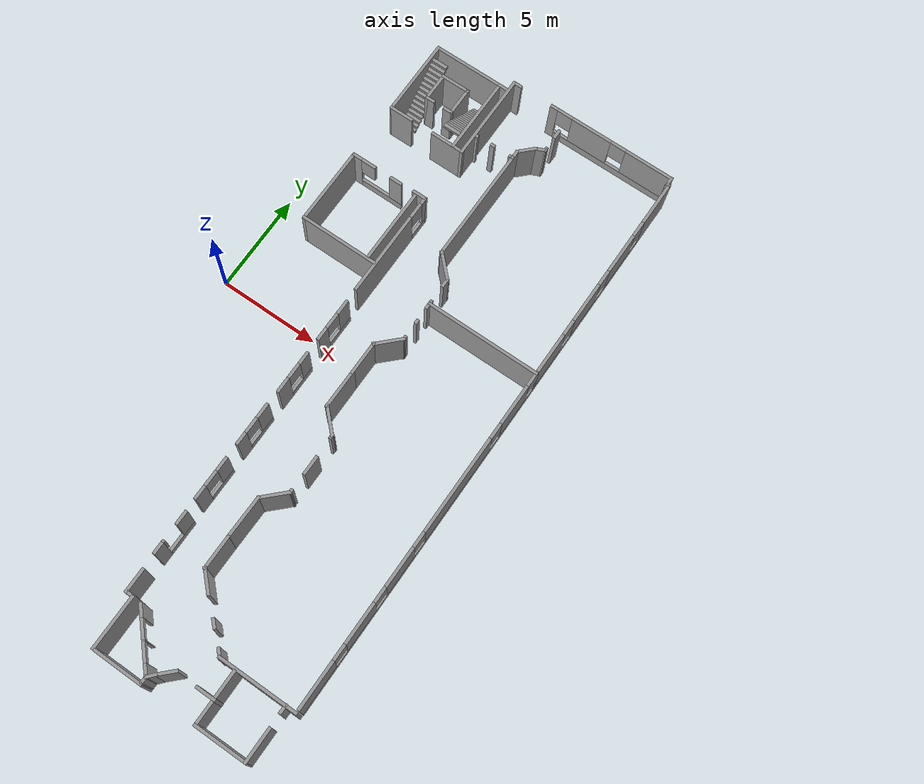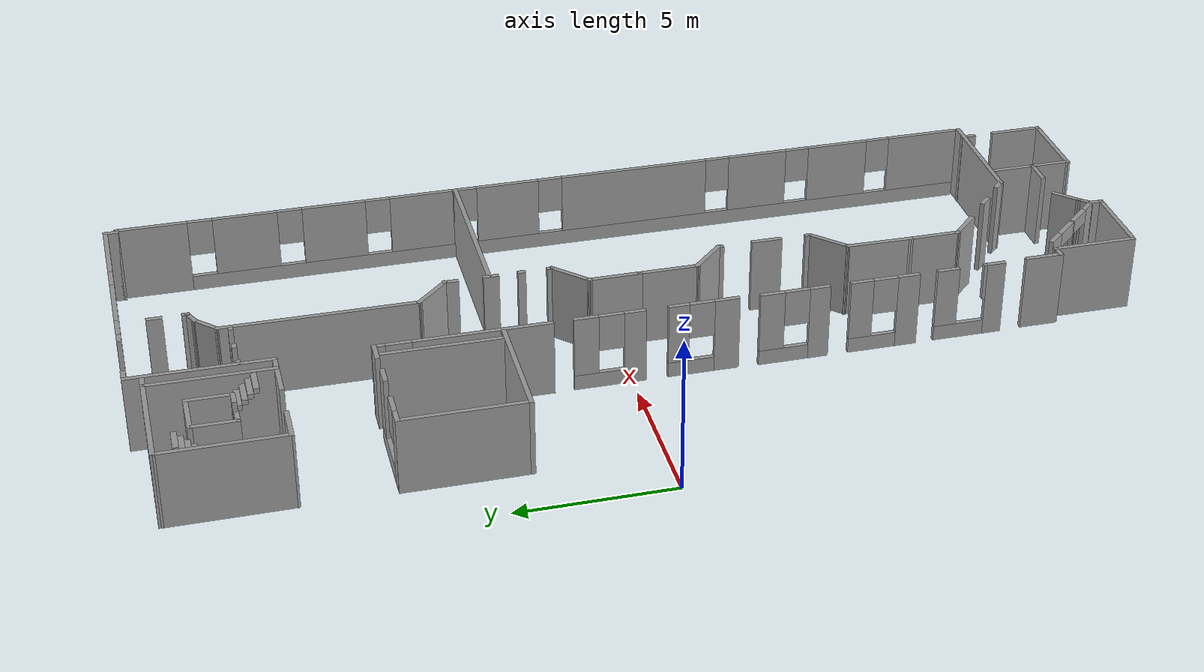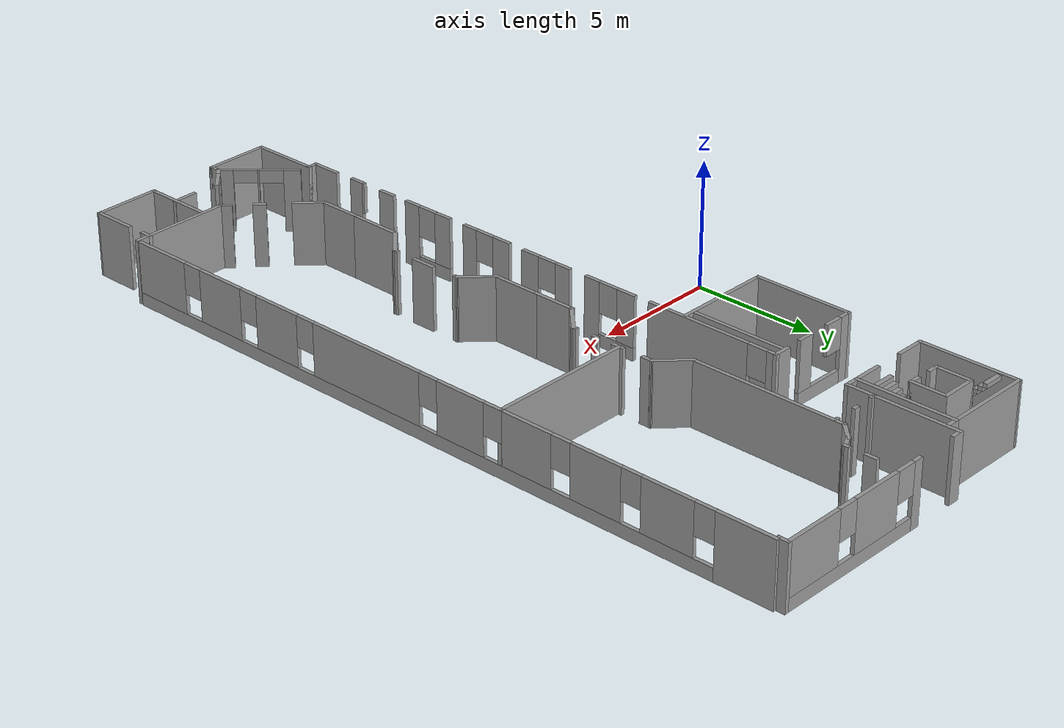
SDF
<?xml version='1.0'?>
<sdf version='1.6'>
  <model name='Parte_DX_(visione_alta_mappa)_CV1'>
    <pose frame=''>8.09528 -0.682905 0 0 -0 0</pose>
    <link name='Stairs_0'>
      <visual name='Stairs_0_Visual_0'>
        <pose frame=''>-5.77033 12.1776 0.083333 0 -0 -3.14159</pose>
        <geometry>
          <box>
            <size>0.790783 0.17667 0.166667</size>
          </box>
        </geometry>
        <material>
          <script>
            <uri>file://media/materials/scripts/gazebo.material</uri>
            <name>Gazebo/Grey</name>
          </script>
          <ambient>1 1 1 1</ambient>
        </material>
      </visual>
      <collision name='Stairs_0_Collision_0'>
        <geometry>
          <box>
            <size>0.790783 0.17667 0.166667</size>
          </box>
        </geometry>
        <pose frame=''>-5.77033 12.1776 0.083333 0 -0 -3.14159</pose>
      </collision>
      <visual name='Stairs_0_Visual_1'>
        <pose frame=''>-5.77033 12.3543 0.25 0 -0 -3.14159</pose>
        <geometry>
          <box>
            <size>0.790783 0.17667 0.166667</size>
          </box>
        </geometry>
        <material>
          <script>
            <uri>file://media/materials/scripts/gazebo.material</uri>
            <name>Gazebo/Grey</name>
          </script>
          <ambient>1 1 1 1</ambient>
        </material>
      </visual>
      <collision name='Stairs_0_Collision_1'>
        <geometry>
          <box>
            <size>0.790783 0.17667 0.166667</size>
          </box>
        </geometry>
        <pose frame=''>-5.77033 12.3543 0.25 0 -0 -3.14159</pose>
      </collision>
      <visual name='Stairs_0_Visual_2'>
        <pose frame=''>-5.77033 12.531 0.416667 0 -0 -3.14159</pose>
        <geometry>
          <box>
            <size>0.790783 0.17667 0.166667</size>
          </box>
        </geometry>
        <material>
          <script>
            <uri>file://media/materials/scripts/gazebo.material</uri>
            <name>Gazebo/Grey</name>
          </script>
          <ambient>1 1 1 1</ambient>
        </material>
      </visual>
      <collision name='Stairs_0_Collision_2'>
        <geometry>
          <box>
            <size>0.790783 0.17667 0.166667</size>
          </box>
        </geometry>
        <pose frame=''>-5.77033 12.531 0.416667 0 -0 -3.14159</pose>
      </collision>
      <visual name='Stairs_0_Visual_3'>
        <pose frame=''>-5.77033 12.7077 0.583333 0 -0 -3.14159</pose>
        <geometry>
          <box>
            <size>0.790783 0.17667 0.166667</size>
          </box>
        </geometry>
        <material>
          <script>
            <uri>file://media/materials/scripts/gazebo.material</uri>
            <name>Gazebo/Grey</name>
          </script>
          <ambient>1 1 1 1</ambient>
        </material>
      </visual>
      <collision name='Stairs_0_Collision_3'>
        <geometry>
          <box>
            <size>0.790783 0.17667 0.166667</size>
          </box>
        </geometry>
        <pose frame=''>-5.77033 12.7077 0.583333 0 -0 -3.14159</pose>
      </collision>
      <visual name='Stairs_0_Visual_4'>
        <pose frame=''>-5.77033 12.8843 0.75 0 -0 -3.14159</pose>
        <geometry>
          <box>
            <size>0.790783 0.17667 0.166667</size>
          </box>
        </geometry>
        <material>
          <script>
            <uri>file://media/materials/scripts/gazebo.material</uri>
            <name>Gazebo/Grey</name>
          </script>
          <ambient>1 1 1 1</ambient>
        </material>
      </visual>
      <collision name='Stairs_0_Collision_4'>
        <geometry>
          <box>
            <size>0.790783 0.17667 0.166667</size>
          </box>
        </geometry>
        <pose frame=''>-5.77033 12.8843 0.75 0 -0 -3.14159</pose>
      </collision>
      <visual name='Stairs_0_Visual_5'>
        <pose frame=''>-5.77033 13.061 0.916667 0 -0 -3.14159</pose>
        <geometry>
          <box>
            <size>0.790783 0.17667 0.166667</size>
          </box>
        </geometry>
        <material>
          <script>
            <uri>file://media/materials/scripts/gazebo.material</uri>
            <name>Gazebo/Grey</name>
          </script>
          <ambient>1 1 1 1</ambient>
        </material>
      </visual>
      <collision name='Stairs_0_Collision_5'>
        <geometry>
          <box>
            <size>0.790783 0.17667 0.166667</size>
          </box>
        </geometry>
        <pose frame=''>-5.77033 13.061 0.916667 0 -0 -3.14159</pose>
      </collision>
      <visual name='Stairs_0_Visual_6'>
        <pose frame=''>-5.77033 13.2377 1.08333 0 -0 -3.14159</pose>
        <geometry>
          <box>
            <size>0.790783 0.17667 0.166667</size>
          </box>
        </geometry>
        <material>
          <script>
            <uri>file://media/materials/scripts/gazebo.material</uri>
            <name>Gazebo/Grey</name>
          </script>
          <ambient>1 1 1 1</ambient>
        </material>
      </visual>
      <collision name='Stairs_0_Collision_6'>
        <geometry>
          <box>
            <size>0.790783 0.17667 0.166667</size>
          </box>
        </geometry>
        <pose frame=''>-5.77033 13.2377 1.08333 0 -0 -3.14159</pose>
      </collision>
      <visual name='Stairs_0_Visual_7'>
        <pose frame=''>-5.77033 13.4143 1.25 0 -0 -3.14159</pose>
        <geometry>
          <box>
            <size>0.790783 0.17667 0.166667</size>
          </box>
        </geometry>
        <material>
          <script>
            <uri>file://media/materials/scripts/gazebo.material</uri>
            <name>Gazebo/Grey</name>
          </script>
          <ambient>1 1 1 1</ambient>
        </material>
      </visual>
      <collision name='Stairs_0_Collision_7'>
        <geometry>
          <box>
            <size>0.790783 0.17667 0.166667</size>
          </box>
        </geometry>
        <pose frame=''>-5.77033 13.4143 1.25 0 -0 -3.14159</pose>
      </collision>
      <visual name='Stairs_0_Visual_8'>
        <pose frame=''>-5.77033 13.591 1.41667 0 -0 -3.14159</pose>
        <geometry>
          <box>
            <size>0.790783 0.17667 0.166667</size>
          </box>
        </geometry>
        <material>
          <script>
            <uri>file://media/materials/scripts/gazebo.material</uri>
            <name>Gazebo/Grey</name>
          </script>
          <ambient>1 1 1 1</ambient>
        </material>
      </visual>
      <collision name='Stairs_0_Collision_8'>
        <geometry>
          <box>
            <size>0.790783 0.17667 0.166667</size>
          </box>
        </geometry>
        <pose frame=''>-5.77033 13.591 1.41667 0 -0 -3.14159</pose>
      </collision>
      <visual name='Stairs_0_Visual_9'>
        <pose frame=''>-5.77033 13.7677 1.58333 0 -0 -3.14159</pose>
        <geometry>
          <box>
            <size>0.790783 0.17667 0.166667</size>
          </box>
        </geometry>
        <material>
          <script>
            <uri>file://media/materials/scripts/gazebo.material</uri>
            <name>Gazebo/Grey</name>
          </script>
          <ambient>1 1 1 1</ambient>
        </material>
      </visual>
      <collision name='Stairs_0_Collision_9'>
        <geometry>
          <box>
            <size>0.790783 0.17667 0.166667</size>
          </box>
        </geometry>
        <pose frame=''>-5.77033 13.7677 1.58333 0 -0 -3.14159</pose>
      </collision>
      <visual name='Stairs_0_Visual_10'>
        <pose frame=''>-5.77033 13.9443 1.75 0 -0 -3.14159</pose>
        <geometry>
          <box>
            <size>0.790783 0.17667 0.166667</size>
          </box>
        </geometry>
        <material>
          <script>
            <uri>file://media/materials/scripts/gazebo.material</uri>
            <name>Gazebo/Grey</name>
          </script>
          <ambient>1 1 1 1</ambient>
        </material>
      </visual>
      <collision name='Stairs_0_Collision_10'>
        <geometry>
          <box>
            <size>0.790783 0.17667 0.166667</size>
          </box>
        </geometry>
        <pose frame=''>-5.77033 13.9443 1.75 0 -0 -3.14159</pose>
      </collision>
      <visual name='Stairs_0_Visual_11'>
        <pose frame=''>-5.77033 14.121 1.91667 0 -0 -3.14159</pose>
        <geometry>
          <box>
            <size>0.790783 0.17667 0.166667</size>
          </box>
        </geometry>
        <material>
          <script>
            <uri>file://media/materials/scripts/gazebo.material</uri>
            <name>Gazebo/Grey</name>
          </script>
          <ambient>1 1 1 1</ambient>
        </material>
      </visual>
      <collision name='Stairs_0_Collision_11'>
        <geometry>
          <box>
            <size>0.790783 0.17667 0.166667</size>
          </box>
        </geometry>
        <pose frame=''>-5.77033 14.121 1.91667 0 -0 -3.14159</pose>
      </collision>
      <visual name='Stairs_0_Visual_12'>
        <pose frame=''>-5.77033 14.2977 2.08333 0 -0 -3.14159</pose>
        <geometry>
          <box>
            <size>0.790783 0.17667 0.166667</size>
          </box>
        </geometry>
        <material>
          <script>
            <uri>file://media/materials/scripts/gazebo.material</uri>
            <name>Gazebo/Grey</name>
          </script>
          <ambient>1 1 1 1</ambient>
        </material>
      </visual>
      <collision name='Stairs_0_Collision_12'>
        <geometry>
          <box>
            <size>0.790783 0.17667 0.166667</size>
          </box>
        </geometry>
        <pose frame=''>-5.77033 14.2977 2.08333 0 -0 -3.14159</pose>
      </collision>
      <visual name='Stairs_0_Visual_13'>
        <pose frame=''>-5.77033 14.4744 2.25 0 -0 -3.14159</pose>
        <geometry>
          <box>
            <size>0.790783 0.17667 0.166667</size>
          </box>
        </geometry>
        <material>
          <script>
            <uri>file://media/materials/scripts/gazebo.material</uri>
            <name>Gazebo/Grey</name>
          </script>
          <ambient>1 1 1 1</ambient>
        </material>
      </visual>
      <collision name='Stairs_0_Collision_13'>
        <geometry>
          <box>
            <size>0.790783 0.17667 0.166667</size>
          </box>
        </geometry>
        <pose frame=''>-5.77033 14.4744 2.25 0 -0 -3.14159</pose>
      </collision>
      <visual name='Stairs_0_Visual_14'>
        <pose frame=''>-5.77033 14.651 2.41667 0 -0 -3.14159</pose>
        <geometry>
          <box>
            <size>0.790783 0.17667 0.166667</size>
          </box>
        </geometry>
        <material>
          <script>
            <uri>file://media/materials/scripts/gazebo.material</uri>
            <name>Gazebo/Grey</name>
          </script>
          <ambient>1 1 1 1</ambient>
        </material>
      </visual>
      <collision name='Stairs_0_Collision_14'>
        <geometry>
          <box>
            <size>0.790783 0.17667 0.166667</size>
          </box>
        </geometry>
        <pose frame=''>-5.77033 14.651 2.41667 0 -0 -3.14159</pose>
      </collision>
    </link>
    <link name='Stairs_1'>
      <visual name='Stairs_1_Visual_0'>
        <pose frame=''>-3.36416 14.6621 0.083333 0 -0 0</pose>
        <geometry>
          <box>
            <size>0.856163 0.179286 0.166667</size>
          </box>
        </geometry>
        <material>
          <script>
            <uri>file://media/materials/scripts/gazebo.material</uri>
            <name>Gazebo/Grey</name>
          </script>
          <ambient>1 1 1 1</ambient>
        </material>
      </visual>
      <collision name='Stairs_1_Collision_0'>
        <geometry>
          <box>
            <size>0.856163 0.179286 0.166667</size>
          </box>
        </geometry>
        <pose frame=''>-3.36416 14.6621 0.083333 0 -0 0</pose>
      </collision>
      <visual name='Stairs_1_Visual_1'>
        <pose frame=''>-3.36416 14.4828 0.25 0 -0 0</pose>
        <geometry>
          <box>
            <size>0.856163 0.179286 0.166667</size>
          </box>
        </geometry>
        <material>
          <script>
            <uri>file://media/materials/scripts/gazebo.material</uri>
            <name>Gazebo/Grey</name>
          </script>
          <ambient>1 1 1 1</ambient>
        </material>
      </visual>
      <collision name='Stairs_1_Collision_1'>
        <geometry>
          <box>
            <size>0.856163 0.179286 0.166667</size>
          </box>
        </geometry>
        <pose frame=''>-3.36416 14.4828 0.25 0 -0 0</pose>
      </collision>
      <visual name='Stairs_1_Visual_2'>
        <pose frame=''>-3.36416 14.3035 0.416667 0 -0 0</pose>
        <geometry>
          <box>
            <size>0.856163 0.179286 0.166667</size>
          </box>
        </geometry>
        <material>
          <script>
            <uri>file://media/materials/scripts/gazebo.material</uri>
            <name>Gazebo/Grey</name>
          </script>
          <ambient>1 1 1 1</ambient>
        </material>
      </visual>
      <collision name='Stairs_1_Collision_2'>
        <geometry>
          <box>
            <size>0.856163 0.179286 0.166667</size>
          </box>
        </geometry>
        <pose frame=''>-3.36416 14.3035 0.416667 0 -0 0</pose>
      </collision>
      <visual name='Stairs_1_Visual_3'>
        <pose frame=''>-3.36416 14.1242 0.583333 0 -0 0</pose>
        <geometry>
          <box>
            <size>0.856163 0.179286 0.166667</size>
          </box>
        </geometry>
        <material>
          <script>
            <uri>file://media/materials/scripts/gazebo.material</uri>
            <name>Gazebo/Grey</name>
          </script>
          <ambient>1 1 1 1</ambient>
        </material>
      </visual>
      <collision name='Stairs_1_Collision_3'>
        <geometry>
          <box>
            <size>0.856163 0.179286 0.166667</size>
          </box>
        </geometry>
        <pose frame=''>-3.36416 14.1242 0.583333 0 -0 0</pose>
      </collision>
      <visual name='Stairs_1_Visual_4'>
        <pose frame=''>-3.36416 13.9449 0.75 0 -0 0</pose>
        <geometry>
          <box>
            <size>0.856163 0.179286 0.166667</size>
          </box>
        </geometry>
        <material>
          <script>
            <uri>file://media/materials/scripts/gazebo.material</uri>
            <name>Gazebo/Grey</name>
          </script>
          <ambient>1 1 1 1</ambient>
        </material>
      </visual>
      <collision name='Stairs_1_Collision_4'>
        <geometry>
          <box>
            <size>0.856163 0.179286 0.166667</size>
          </box>
        </geometry>
        <pose frame=''>-3.36416 13.9449 0.75 0 -0 0</pose>
      </collision>
      <visual name='Stairs_1_Visual_5'>
        <pose frame=''>-3.36416 13.7656 0.916667 0 -0 0</pose>
        <geometry>
          <box>
            <size>0.856163 0.179286 0.166667</size>
          </box>
        </geometry>
        <material>
          <script>
            <uri>file://media/materials/scripts/gazebo.material</uri>
            <name>Gazebo/Grey</name>
          </script>
          <ambient>1 1 1 1</ambient>
        </material>
      </visual>
      <collision name='Stairs_1_Collision_5'>
        <geometry>
          <box>
            <size>0.856163 0.179286 0.166667</size>
          </box>
        </geometry>
        <pose frame=''>-3.36416 13.7656 0.916667 0 -0 0</pose>
      </collision>
      <visual name='Stairs_1_Visual_6'>
        <pose frame=''>-3.36416 13.5863 1.08333 0 -0 0</pose>
        <geometry>
          <box>
            <size>0.856163 0.179286 0.166667</size>
          </box>
        </geometry>
        <material>
          <script>
            <uri>file://media/materials/scripts/gazebo.material</uri>
            <name>Gazebo/Grey</name>
          </script>
          <ambient>1 1 1 1</ambient>
        </material>
      </visual>
      <collision name='Stairs_1_Collision_6'>
        <geometry>
          <box>
            <size>0.856163 0.179286 0.166667</size>
          </box>
        </geometry>
        <pose frame=''>-3.36416 13.5863 1.08333 0 -0 0</pose>
      </collision>
      <visual name='Stairs_1_Visual_7'>
        <pose frame=''>-3.36416 13.4071 1.25 0 -0 0</pose>
        <geometry>
          <box>
            <size>0.856163 0.179286 0.166667</size>
          </box>
        </geometry>
        <material>
          <script>
            <uri>file://media/materials/scripts/gazebo.material</uri>
            <name>Gazebo/Grey</name>
          </script>
          <ambient>1 1 1 1</ambient>
        </material>
      </visual>
      <collision name='Stairs_1_Collision_7'>
        <geometry>
          <box>
            <size>0.856163 0.179286 0.166667</size>
          </box>
        </geometry>
        <pose frame=''>-3.36416 13.4071 1.25 0 -0 0</pose>
      </collision>
      <visual name='Stairs_1_Visual_8'>
        <pose frame=''>-3.36416 13.2278 1.41667 0 -0 0</pose>
        <geometry>
          <box>
            <size>0.856163 0.179286 0.166667</size>
          </box>
        </geometry>
        <material>
          <script>
            <uri>file://media/materials/scripts/gazebo.material</uri>
            <name>Gazebo/Grey</name>
          </script>
          <ambient>1 1 1 1</ambient>
        </material>
      </visual>
      <collision name='Stairs_1_Collision_8'>
        <geometry>
          <box>
            <size>0.856163 0.179286 0.166667</size>
          </box>
        </geometry>
        <pose frame=''>-3.36416 13.2278 1.41667 0 -0 0</pose>
      </collision>
      <visual name='Stairs_1_Visual_9'>
        <pose frame=''>-3.36416 13.0485 1.58333 0 -0 0</pose>
        <geometry>
          <box>
            <size>0.856163 0.179286 0.166667</size>
          </box>
        </geometry>
        <material>
          <script>
            <uri>file://media/materials/scripts/gazebo.material</uri>
            <name>Gazebo/Grey</name>
          </script>
          <ambient>1 1 1 1</ambient>
        </material>
      </visual>
      <collision name='Stairs_1_Collision_9'>
        <geometry>
          <box>
            <size>0.856163 0.179286 0.166667</size>
          </box>
        </geometry>
        <pose frame=''>-3.36416 13.0485 1.58333 0 -0 0</pose>
      </collision>
      <visual name='Stairs_1_Visual_10'>
        <pose frame=''>-3.36416 12.8692 1.75 0 -0 0</pose>
        <geometry>
          <box>
            <size>0.856163 0.179286 0.166667</size>
          </box>
        </geometry>
        <material>
          <script>
            <uri>file://media/materials/scripts/gazebo.material</uri>
            <name>Gazebo/Grey</name>
          </script>
          <ambient>1 1 1 1</ambient>
        </material>
      </visual>
      <collision name='Stairs_1_Collision_10'>
        <geometry>
          <box>
            <size>0.856163 0.179286 0.166667</size>
          </box>
        </geometry>
        <pose frame=''>-3.36416 12.8692 1.75 0 -0 0</pose>
      </collision>
      <visual name='Stairs_1_Visual_11'>
        <pose frame=''>-3.36416 12.6899 1.91667 0 -0 0</pose>
        <geometry>
          <box>
            <size>0.856163 0.179286 0.166667</size>
          </box>
        </geometry>
        <material>
          <script>
            <uri>file://media/materials/scripts/gazebo.material</uri>
            <name>Gazebo/Grey</name>
          </script>
          <ambient>1 1 1 1</ambient>
        </material>
      </visual>
      <collision name='Stairs_1_Collision_11'>
        <geometry>
          <box>
            <size>0.856163 0.179286 0.166667</size>
          </box>
        </geometry>
        <pose frame=''>-3.36416 12.6899 1.91667 0 -0 0</pose>
      </collision>
      <visual name='Stairs_1_Visual_12'>
        <pose frame=''>-3.36416 12.5106 2.08333 0 -0 0</pose>
        <geometry>
          <box>
            <size>0.856163 0.179286 0.166667</size>
          </box>
        </geometry>
        <material>
          <script>
            <uri>file://media/materials/scripts/gazebo.material</uri>
            <name>Gazebo/Grey</name>
          </script>
          <ambient>1 1 1 1</ambient>
        </material>
      </visual>
      <collision name='Stairs_1_Collision_12'>
        <geometry>
          <box>
            <size>0.856163 0.179286 0.166667</size>
          </box>
        </geometry>
        <pose frame=''>-3.36416 12.5106 2.08333 0 -0 0</pose>
      </collision>
      <visual name='Stairs_1_Visual_13'>
        <pose frame=''>-3.36416 12.3313 2.25 0 -0 0</pose>
        <geometry>
          <box>
            <size>0.856163 0.179286 0.166667</size>
          </box>
        </geometry>
        <material>
          <script>
            <uri>file://media/materials/scripts/gazebo.material</uri>
            <name>Gazebo/Grey</name>
          </script>
          <ambient>1 1 1 1</ambient>
        </material>
      </visual>
      <collision name='Stairs_1_Collision_13'>
        <geometry>
          <box>
            <size>0.856163 0.179286 0.166667</size>
          </box>
        </geometry>
        <pose frame=''>-3.36416 12.3313 2.25 0 -0 0</pose>
      </collision>
      <visual name='Stairs_1_Visual_14'>
        <pose frame=''>-3.36416 12.1521 2.41667 0 -0 0</pose>
        <geometry>
          <box>
            <size>0.856163 0.179286 0.166667</size>
          </box>
        </geometry>
        <material>
          <script>
            <uri>file://media/materials/scripts/gazebo.material</uri>
            <name>Gazebo/Grey</name>
          </script>
          <ambient>1 1 1 1</ambient>
        </material>
      </visual>
      <collision name='Stairs_1_Collision_14'>
        <geometry>
          <box>
            <size>0.856163 0.179286 0.166667</size>
          </box>
        </geometry>
        <pose frame=''>-3.36416 12.1521 2.41667 0 -0 0</pose>
      </collision>
    </link>
    <link name='Wall_0'>
      <collision name='Wall_0_Collision'>
        <geometry>
          <box>
            <size>3.5 0.15 2.5</size>
          </box>
        </geometry>
        <pose frame=''>0 0 1.25 0 -0 0</pose>
      </collision>
      <visual name='Wall_0_Visual'>
        <pose frame=''>0 0 1.25 0 -0 0</pose>
        <geometry>
          <box>
            <size>3.5 0.15 2.5</size>
          </box>
        </geometry>
        <material>
          <script>
            <uri>file://media/materials/scripts/gazebo.material</uri>
            <name>Gazebo/Grey</name>
          </script>
          <ambient>1 1 1 1</ambient>
        </material>
      </visual>
      <pose frame=''>-4.6353 15.3082 0 0 -0 0</pose>
    </link>
    <link name='Wall_101'>
      <collision name='Wall_101_Collision'>
        <geometry>
          <box>
            <size>1.75 0.15 2.5</size>
          </box>
        </geometry>
        <pose frame=''>0 0 1.25 0 -0 0</pose>
      </collision>
      <visual name='Wall_101_Visual'>
        <pose frame=''>0 0 1.25 0 -0 0</pose>
        <geometry>
          <box>
            <size>1.75 0.15 2.5</size>
          </box>
        </geometry>
        <material>
          <script>
            <uri>file://media/materials/scripts/gazebo.material</uri>
            <name>Gazebo/Grey</name>
          </script>
          <ambient>1 1 1 1</ambient>
        </material>
      </visual>
      <pose frame=''>-0.253384 0.713118 0 0 0 -1.5708</pose>
    </link>
    <link name='Wall_103'>
      <collision name='Wall_103_Collision'>
        <geometry>
          <box>
            <size>2 0.15 2.5</size>
          </box>
        </geometry>
        <pose frame=''>0 0 1.25 0 -0 0</pose>
      </collision>
      <visual name='Wall_103_Visual'>
        <pose frame=''>0 0 1.25 0 -0 0</pose>
        <geometry>
          <box>
            <size>2 0.15 2.5</size>
          </box>
        </geometry>
        <material>
          <script>
            <uri>file://media/materials/scripts/gazebo.material</uri>
            <name>Gazebo/Grey</name>
          </script>
          <ambient>1 1 1 1</ambient>
        </material>
      </visual>
      <pose frame=''>-0.253384 -1.01188 0 0 0 -1.5708</pose>
    </link>
    <link name='Wall_105'>
      <collision name='Wall_105_Collision'>
        <geometry>
          <box>
            <size>1.5 0.15 2.5</size>
          </box>
        </geometry>
        <pose frame=''>0 0 1.25 0 -0 0</pose>
      </collision>
      <visual name='Wall_105_Visual'>
        <pose frame=''>0 0 1.25 0 -0 0</pose>
        <geometry>
          <box>
            <size>1.5 0.15 2.5</size>
          </box>
        </geometry>
        <material>
          <script>
            <uri>file://media/materials/scripts/gazebo.material</uri>
            <name>Gazebo/Grey</name>
          </script>
          <ambient>1 1 1 1</ambient>
        </material>
      </visual>
      <pose frame=''>0.223913 -2.41418 0 0 0 -0.785398</pose>
    </link>
    <link name='Wall_106'>
      <collision name='Wall_106_Collision'>
        <geometry>
          <box>
            <size>0.25 0.15 2.5</size>
          </box>
        </geometry>
        <pose frame=''>0 0 1.25 0 -0 0</pose>
      </collision>
      <visual name='Wall_106_Visual'>
        <pose frame=''>0 0 1.25 0 -0 0</pose>
        <geometry>
          <box>
            <size>0.25 0.15 2.5</size>
          </box>
        </geometry>
        <material>
          <script>
            <uri>file://media/materials/scripts/gazebo.material</uri>
            <name>Gazebo/Grey</name>
          </script>
          <ambient>1 1 1 1</ambient>
        </material>
      </visual>
      <pose frame=''>0.70121 -2.94148 0 0 0 -1.5708</pose>
    </link>
    <link name='Wall_108'>
      <collision name='Wall_108_Collision'>
        <geometry>
          <box>
            <size>1 0.15 2.5</size>
          </box>
        </geometry>
        <pose frame=''>0 0 1.25 0 -0 0</pose>
      </collision>
      <visual name='Wall_108_Visual'>
        <pose frame=''>0 0 1.25 0 -0 0</pose>
        <geometry>
          <box>
            <size>1 0.15 2.5</size>
          </box>
        </geometry>
        <material>
          <script>
            <uri>file://media/materials/scripts/gazebo.material</uri>
            <name>Gazebo/Grey</name>
          </script>
          <ambient>1 1 1 1</ambient>
        </material>
      </visual>
      <pose frame=''>0.723822 -4.48667 0 0 0 -1.5708</pose>
    </link>
    <link name='Wall_110'>
      <collision name='Wall_110_Collision'>
        <geometry>
          <box>
            <size>0.25 0.15 2.5</size>
          </box>
        </geometry>
        <pose frame=''>0 0 1.25 0 -0 0</pose>
      </collision>
      <visual name='Wall_110_Visual'>
        <pose frame=''>0 0 1.25 0 -0 0</pose>
        <geometry>
          <box>
            <size>0.25 0.15 2.5</size>
          </box>
        </geometry>
        <material>
          <script>
            <uri>file://media/materials/scripts/gazebo.material</uri>
            <name>Gazebo/Grey</name>
          </script>
          <ambient>1 1 1 1</ambient>
        </material>
      </visual>
      <pose frame=''>0.706863 -5.87545 0 0 0 -1.5708</pose>
    </link>
    <link name='Wall_111'>
      <collision name='Wall_111_Collision'>
        <geometry>
          <box>
            <size>1.5 0.15 2.5</size>
          </box>
        </geometry>
        <pose frame=''>0 0 1.25 0 -0 0</pose>
      </collision>
      <visual name='Wall_111_Visual'>
        <pose frame=''>0 0 1.25 0 -0 0</pose>
        <geometry>
          <box>
            <size>1.5 0.15 2.5</size>
          </box>
        </geometry>
        <material>
          <script>
            <uri>file://media/materials/scripts/gazebo.material</uri>
            <name>Gazebo/Grey</name>
          </script>
          <ambient>1 1 1 1</ambient>
        </material>
      </visual>
      <pose frame=''>0.229566 -6.40275 0 0 0 -2.35619</pose>
    </link>
    <link name='Wall_113'>
      <collision name='Wall_113_Collision'>
        <geometry>
          <box>
            <size>2.21308 0.15 2.5</size>
          </box>
        </geometry>
        <pose frame=''>0 0 1.25 0 -0 0</pose>
      </collision>
      <visual name='Wall_113_Visual'>
        <pose frame=''>0 0 1.25 0 -0 0</pose>
        <geometry>
          <box>
            <size>2.21308 0.15 2.5</size>
          </box>
        </geometry>
        <material>
          <script>
            <uri>file://media/materials/scripts/gazebo.material</uri>
            <name>Gazebo/Grey</name>
          </script>
          <ambient>1 1 1 1</ambient>
        </material>
      </visual>
      <pose frame=''>-0.262289 -7.91149 0 0 0 -1.58491</pose>
    </link>
    <link name='Wall_117'>
      <collision name='Wall_117_Collision'>
        <geometry>
          <box>
            <size>0.15 0.15 2.5</size>
          </box>
        </geometry>
        <pose frame=''>0 0 1.25 0 -0 0</pose>
      </collision>
      <visual name='Wall_117_Visual'>
        <pose frame=''>0 0 1.25 0 -0 0</pose>
        <geometry>
          <box>
            <size>0.15 0.15 2.5</size>
          </box>
        </geometry>
        <material>
          <script>
            <uri>file://media/materials/scripts/gazebo.material</uri>
            <name>Gazebo/Grey</name>
          </script>
          <ambient>1 1 1 1</ambient>
        </material>
      </visual>
      <pose frame=''>-0.253384 1.51312 0 0 -0 0</pose>
    </link>
    <link name='Wall_119'>
      <collision name='Wall_119_Collision'>
        <geometry>
          <box>
            <size>0.25 0.15 2.5</size>
          </box>
        </geometry>
        <pose frame=''>0 0 1.25 0 -0 0</pose>
      </collision>
      <visual name='Wall_119_Visual'>
        <pose frame=''>0 0 1.25 0 -0 0</pose>
        <geometry>
          <box>
            <size>0.25 0.15 2.5</size>
          </box>
        </geometry>
        <material>
          <script>
            <uri>file://media/materials/scripts/gazebo.material</uri>
            <name>Gazebo/Grey</name>
          </script>
          <ambient>1 1 1 1</ambient>
        </material>
      </visual>
      <pose frame=''>0.70121 2.51771 0 0 -0 1.5708</pose>
    </link>
    <link name='Wall_123'>
      <collision name='Wall_123_Collision'>
        <geometry>
          <box>
            <size>1.5 0.15 2.5</size>
          </box>
        </geometry>
        <pose frame=''>0 0 1.25 0 -0 0</pose>
      </collision>
      <visual name='Wall_123_Visual'>
        <pose frame=''>0 0 1.25 0 -0 0</pose>
        <geometry>
          <box>
            <size>1.5 0.15 2.5</size>
          </box>
        </geometry>
        <material>
          <script>
            <uri>file://media/materials/scripts/gazebo.material</uri>
            <name>Gazebo/Grey</name>
          </script>
          <ambient>1 1 1 1</ambient>
        </material>
      </visual>
      <pose frame=''>0.223913 1.99042 0 0 -0 0.785398</pose>
    </link>
    <link name='Wall_125'>
      <collision name='Wall_125_Collision'>
        <geometry>
          <box>
            <size>0.25 0.15 2.5</size>
          </box>
        </geometry>
        <pose frame=''>0 0 1.25 0 -0 0</pose>
      </collision>
      <visual name='Wall_125_Visual'>
        <pose frame=''>0 0 1.25 0 -0 0</pose>
        <geometry>
          <box>
            <size>0.25 0.15 2.5</size>
          </box>
        </geometry>
        <material>
          <script>
            <uri>file://media/materials/scripts/gazebo.material</uri>
            <name>Gazebo/Grey</name>
          </script>
          <ambient>1 1 1 1</ambient>
        </material>
      </visual>
      <pose frame=''>0.700925 3.44587 0 0 0 -1.5708</pose>
    </link>
    <link name='Wall_127'>
      <collision name='Wall_127_Collision'>
        <geometry>
          <box>
            <size>0.5 0.15 2.5</size>
          </box>
        </geometry>
        <pose frame=''>0 0 1.25 0 -0 0</pose>
      </collision>
      <visual name='Wall_127_Visual'>
        <pose frame=''>0 0 1.25 0 -0 0</pose>
        <geometry>
          <box>
            <size>0.5 0.15 2.5</size>
          </box>
        </geometry>
        <material>
          <script>
            <uri>file://media/materials/scripts/gazebo.material</uri>
            <name>Gazebo/Grey</name>
          </script>
          <ambient>1 1 1 1</ambient>
        </material>
      </visual>
      <pose frame=''>0.681262 4.41709 0 0 0 -1.5708</pose>
    </link>
    <link name='Wall_130'>
      <collision name='Wall_130_Collision'>
        <geometry>
          <box>
            <size>5.75 0.15 2.5</size>
          </box>
        </geometry>
        <pose frame=''>0 0 1.25 0 -0 0</pose>
      </collision>
      <visual name='Wall_130_Visual'>
        <pose frame=''>0 0 1.25 0 -0 0</pose>
        <geometry>
          <box>
            <size>5.75 0.15 2.5</size>
          </box>
        </geometry>
        <material>
          <script>
            <uri>file://media/materials/scripts/gazebo.material</uri>
            <name>Gazebo/Grey</name>
          </script>
          <ambient>1 1 1 1</ambient>
        </material>
      </visual>
      <pose frame=''>3.51474 4.4692 0 0 -0 3.14159</pose>
    </link>
    <link name='Wall_132'>
      <collision name='Wall_132_Collision'>
        <geometry>
          <box>
            <size>0.25 0.15 2.5</size>
          </box>
        </geometry>
        <pose frame=''>0 0 1.25 0 -0 0</pose>
      </collision>
      <visual name='Wall_132_Visual'>
        <pose frame=''>0 0 1.25 0 -0 0</pose>
        <geometry>
          <box>
            <size>0.25 0.15 2.5</size>
          </box>
        </geometry>
        <material>
          <script>
            <uri>file://media/materials/scripts/gazebo.material</uri>
            <name>Gazebo/Grey</name>
          </script>
          <ambient>1 1 1 1</ambient>
        </material>
      </visual>
      <pose frame=''>-1.36627 12.5347 0 0 -0 0</pose>
    </link>
    <link name='Wall_134'>
      <collision name='Wall_134_Collision'>
        <geometry>
          <box>
            <size>0.25 0.15 2.5</size>
          </box>
        </geometry>
        <pose frame=''>0 0 1.25 0 -0 0</pose>
      </collision>
      <visual name='Wall_134_Visual'>
        <pose frame=''>0 0 1.25 0 -0 0</pose>
        <geometry>
          <box>
            <size>0.25 0.15 2.5</size>
          </box>
        </geometry>
        <material>
          <script>
            <uri>file://media/materials/scripts/gazebo.material</uri>
            <name>Gazebo/Grey</name>
          </script>
          <ambient>1 1 1 1</ambient>
        </material>
      </visual>
      <pose frame=''>-0.351158 12.5347 0 0 -0 3.14159</pose>
    </link>
    <link name='Wall_136'>
      <collision name='Wall_136_Collision'>
        <geometry>
          <box>
            <size>0.25 0.15 2.5</size>
          </box>
        </geometry>
        <pose frame=''>0 0 1.25 0 -0 0</pose>
      </collision>
      <visual name='Wall_136_Visual'>
        <pose frame=''>0 0 1.25 0 -0 0</pose>
        <geometry>
          <box>
            <size>0.25 0.15 2.5</size>
          </box>
        </geometry>
        <material>
          <script>
            <uri>file://media/materials/scripts/gazebo.material</uri>
            <name>Gazebo/Grey</name>
          </script>
          <ambient>1 1 1 1</ambient>
        </material>
      </visual>
      <pose frame=''>-2.28438 12.5087 0 0 -0 0</pose>
    </link>
    <link name='Wall_138'>
      <collision name='Wall_138_Collision'>
        <geometry>
          <box>
            <size>0.5 0.15 2.5</size>
          </box>
        </geometry>
        <pose frame=''>0 0 1.25 0 -0 0</pose>
      </collision>
      <visual name='Wall_138_Visual'>
        <pose frame=''>0 0 1.25 0 -0 0</pose>
        <geometry>
          <box>
            <size>0.5 0.15 2.5</size>
          </box>
        </geometry>
        <material>
          <script>
            <uri>file://media/materials/scripts/gazebo.material</uri>
            <name>Gazebo/Grey</name>
          </script>
          <ambient>1 1 1 1</ambient>
        </material>
      </visual>
      <pose frame=''>5.78705 -13.262 0 0 0 -1.5708</pose>
    </link>
    <link name='Wall_140'>
      <collision name='Wall_140_Collision'>
        <geometry>
          <box>
            <size>1.75 0.15 2.5</size>
          </box>
        </geometry>
        <pose frame=''>0 0 1.25 0 -0 0</pose>
      </collision>
      <visual name='Wall_140_Visual'>
        <pose frame=''>0 0 1.25 0 -0 0</pose>
        <geometry>
          <box>
            <size>1.75 0.15 2.5</size>
          </box>
        </geometry>
        <material>
          <script>
            <uri>file://media/materials/scripts/gazebo.material</uri>
            <name>Gazebo/Grey</name>
          </script>
          <ambient>1 1 1 1</ambient>
        </material>
      </visual>
      <pose frame=''>5.79565 -14.9955 0 0 0 -1.5708</pose>
    </link>
    <link name='Wall_142'>
      <collision name='Wall_142_Collision'>
        <geometry>
          <box>
            <size>2.75 0.15 2.5</size>
          </box>
        </geometry>
        <pose frame=''>0 0 1.25 0 -0 0</pose>
      </collision>
      <visual name='Wall_142_Visual'>
        <pose frame=''>0 0 1.25 0 -0 0</pose>
        <geometry>
          <box>
            <size>2.75 0.15 2.5</size>
          </box>
        </geometry>
        <material>
          <script>
            <uri>file://media/materials/scripts/gazebo.material</uri>
            <name>Gazebo/Grey</name>
          </script>
          <ambient>1 1 1 1</ambient>
        </material>
      </visual>
      <pose frame=''>3.27651 -14.5074 0 0 0 -1.5708</pose>
    </link>
    <link name='Wall_143'>
      <collision name='Wall_143_Collision'>
        <geometry>
          <box>
            <size>2.66916 0.15 2.5</size>
          </box>
        </geometry>
        <pose frame=''>0 0 1.25 0 -0 0</pose>
      </collision>
      <visual name='Wall_143_Visual'>
        <pose frame=''>0 0 1.25 0 -0 0</pose>
        <geometry>
          <box>
            <size>2.66916 0.15 2.5</size>
          </box>
        </geometry>
        <material>
          <script>
            <uri>file://media/materials/scripts/gazebo.material</uri>
            <name>Gazebo/Grey</name>
          </script>
          <ambient>1 1 1 1</ambient>
        </material>
      </visual>
      <pose frame=''>4.53608 -15.8014 0 0 -0 0.004735</pose>
    </link>
    <link name='Wall_145'>
      <collision name='Wall_145_Collision'>
        <geometry>
          <box>
            <size>1 0.15 2.5</size>
          </box>
        </geometry>
        <pose frame=''>0 0 1.25 0 -0 0</pose>
      </collision>
      <visual name='Wall_145_Visual'>
        <pose frame=''>0 0 1.25 0 -0 0</pose>
        <geometry>
          <box>
            <size>1 0.15 2.5</size>
          </box>
        </geometry>
        <material>
          <script>
            <uri>file://media/materials/scripts/gazebo.material</uri>
            <name>Gazebo/Grey</name>
          </script>
          <ambient>1 1 1 1</ambient>
        </material>
      </visual>
      <pose frame=''>2.86011 -14.5744 0 0 -0 3.14159</pose>
    </link>
    <link name='Wall_147'>
      <collision name='Wall_147_Collision'>
        <geometry>
          <box>
            <size>1 0.15 2.5</size>
          </box>
        </geometry>
        <pose frame=''>0 0 1.25 0 -0 0</pose>
      </collision>
      <visual name='Wall_147_Visual'>
        <pose frame=''>0 0 1.25 0 -0 0</pose>
        <geometry>
          <box>
            <size>1 0.15 2.5</size>
          </box>
        </geometry>
        <material>
          <script>
            <uri>file://media/materials/scripts/gazebo.material</uri>
            <name>Gazebo/Grey</name>
          </script>
          <ambient>1 1 1 1</ambient>
        </material>
      </visual>
      <pose frame=''>1.0501 -14.8406 0 0 0 -2.35619</pose>
    </link>
    <link name='Wall_150'>
      <collision name='Wall_150_Collision'>
        <geometry>
          <box>
            <size>2.5 0.15 2.5</size>
          </box>
        </geometry>
        <pose frame=''>0 0 1.25 0 -0 0</pose>
      </collision>
      <visual name='Wall_150_Visual'>
        <pose frame=''>0 0 1.25 0 -0 0</pose>
        <geometry>
          <box>
            <size>2.5 0.15 2.5</size>
          </box>
        </geometry>
        <material>
          <script>
            <uri>file://media/materials/scripts/gazebo.material</uri>
            <name>Gazebo/Grey</name>
          </script>
          <ambient>1 1 1 1</ambient>
        </material>
      </visual>
      <pose frame=''>-0.698526 -15.7953 0 0 -0 0</pose>
    </link>
    <link name='Wall_151'>
      <collision name='Wall_151_Collision'>
        <geometry>
          <box>
            <size>0.15 0.15 2.5</size>
          </box>
        </geometry>
        <pose frame=''>0 0 1.25 0 -0 0</pose>
      </collision>
      <visual name='Wall_151_Visual'>
        <pose frame=''>0 0 1.25 0 -0 0</pose>
        <geometry>
          <box>
            <size>0.15 0.15 2.5</size>
          </box>
        </geometry>
        <material>
          <script>
            <uri>file://media/materials/scripts/gazebo.material</uri>
            <name>Gazebo/Grey</name>
          </script>
          <ambient>1 1 1 1</ambient>
        </material>
      </visual>
      <pose frame=''>0.485072 -15.7953 0 0 -0 0</pose>
    </link>
    <link name='Wall_154'>
      <collision name='Wall_154_Collision'>
        <geometry>
          <box>
            <size>0.5 0.15 2.5</size>
          </box>
        </geometry>
        <pose frame=''>0 0 1.25 0 -0 0</pose>
      </collision>
      <visual name='Wall_154_Visual'>
        <pose frame=''>0 0 1.25 0 -0 0</pose>
        <geometry>
          <box>
            <size>0.5 0.15 2.5</size>
          </box>
        </geometry>
        <material>
          <script>
            <uri>file://media/materials/scripts/gazebo.material</uri>
            <name>Gazebo/Grey</name>
          </script>
          <ambient>1 1 1 1</ambient>
        </material>
      </visual>
      <pose frame=''>0.485072 -15.6203 0 0 -0 1.5708</pose>
    </link>
    <link name='Wall_155'>
      <collision name='Wall_155_Collision'>
        <geometry>
          <box>
            <size>0.553138 0.15 2.5</size>
          </box>
        </geometry>
        <pose frame=''>0 0 1.25 0 -0 0</pose>
      </collision>
      <visual name='Wall_155_Visual'>
        <pose frame=''>0 0 1.25 0 -0 0</pose>
        <geometry>
          <box>
            <size>0.553138 0.15 2.5</size>
          </box>
        </geometry>
        <material>
          <script>
            <uri>file://media/materials/scripts/gazebo.material</uri>
            <name>Gazebo/Grey</name>
          </script>
          <ambient>1 1 1 1</ambient>
        </material>
      </visual>
      <pose frame=''>0.617326 -15.2932 0 0 -0 0.85512</pose>
    </link>
    <link name='Wall_157'>
      <collision name='Wall_157_Collision'>
        <geometry>
          <box>
            <size>2.75 0.15 2.5</size>
          </box>
        </geometry>
        <pose frame=''>0 0 1.25 0 -0 0</pose>
      </collision>
      <visual name='Wall_157_Visual'>
        <pose frame=''>0 0 1.25 0 -0 0</pose>
        <geometry>
          <box>
            <size>2.75 0.15 2.5</size>
          </box>
        </geometry>
        <material>
          <script>
            <uri>file://media/materials/scripts/gazebo.material</uri>
            <name>Gazebo/Grey</name>
          </script>
          <ambient>1 1 1 1</ambient>
        </material>
      </visual>
      <pose frame=''>-1.9853 -14.4816 0 0 0 -1.5708</pose>
    </link>
    <link name='Wall_160'>
      <collision name='Wall_160_Collision'>
        <geometry>
          <box>
            <size>0.5 0.15 2.5</size>
          </box>
        </geometry>
        <pose frame=''>0 0 1.25 0 -0 0</pose>
      </collision>
      <visual name='Wall_160_Visual'>
        <pose frame=''>0 0 1.25 0 -0 0</pose>
        <geometry>
          <box>
            <size>0.5 0.15 2.5</size>
          </box>
        </geometry>
        <material>
          <script>
            <uri>file://media/materials/scripts/gazebo.material</uri>
            <name>Gazebo/Grey</name>
          </script>
          <ambient>1 1 1 1</ambient>
        </material>
      </visual>
      <pose frame=''>-2.1603 -13.1816 0 0 -0 3.14159</pose>
    </link>
    <link name='Wall_162'>
      <collision name='Wall_162_Collision'>
        <geometry>
          <box>
            <size>1.25 0.15 2.5</size>
          </box>
        </geometry>
        <pose frame=''>0 0 1.25 0 -0 0</pose>
      </collision>
      <visual name='Wall_162_Visual'>
        <pose frame=''>0 0 1.25 0 -0 0</pose>
        <geometry>
          <box>
            <size>1.25 0.15 2.5</size>
          </box>
        </geometry>
        <material>
          <script>
            <uri>file://media/materials/scripts/gazebo.material</uri>
            <name>Gazebo/Grey</name>
          </script>
          <ambient>1 1 1 1</ambient>
        </material>
      </visual>
      <pose frame=''>-2.3378 -12.6298 0 0 0 -1.5708</pose>
    </link>
    <link name='Wall_168'>
      <pose frame=''>-2.37767 -10.186 0 0 -0 1.5708</pose>
      <visual name='Wall_168_Visual_0'>
        <pose frame=''>-0.818759 0 1.25 0 -0 0</pose>
        <geometry>
          <box>
            <size>0.612482 0.15 2.5</size>
          </box>
        </geometry>
        <material>
          <script>
            <uri>file://media/materials/scripts/gazebo.material</uri>
            <name>Gazebo/Grey</name>
          </script>
          <ambient>1 1 1 1</ambient>
        </material>
      </visual>
      <collision name='Wall_168_Collision_0'>
        <geometry>
          <box>
            <size>0.612482 0.15 2.5</size>
          </box>
        </geometry>
        <pose frame=''>-0.818759 0 1.25 0 -0 0</pose>
      </collision>
      <visual name='Wall_168_Visual_1'>
        <pose frame=''>0.306241 0 0.25 0 -0 0</pose>
        <geometry>
          <box>
            <size>1.63752 0.15 0.5</size>
          </box>
        </geometry>
        <material>
          <script>
            <uri>file://media/materials/scripts/gazebo.material</uri>
            <name>Gazebo/Grey</name>
          </script>
          <ambient>1 1 1 1</ambient>
        </material>
      </visual>
      <collision name='Wall_168_Collision_1'>
        <geometry>
          <box>
            <size>1.63752 0.15 0.5</size>
          </box>
        </geometry>
        <pose frame=''>0.306241 0 0.25 0 -0 0</pose>
      </collision>
      <visual name='Wall_168_Visual_2'>
        <pose frame=''>0.760521 0 1.5 0 -0 0</pose>
        <geometry>
          <box>
            <size>0.728959 0.15 2</size>
          </box>
        </geometry>
        <material>
          <script>
            <uri>file://media/materials/scripts/gazebo.material</uri>
            <name>Gazebo/Grey</name>
          </script>
          <ambient>1 1 1 1</ambient>
        </material>
      </visual>
      <collision name='Wall_168_Collision_2'>
        <geometry>
          <box>
            <size>0.728959 0.15 2</size>
          </box>
        </geometry>
        <pose frame=''>0.760521 0 1.5 0 -0 0</pose>
      </collision>
      <visual name='Wall_168_Visual_3'>
        <pose frame=''>-0.458239 0 1.9 0 -0 0</pose>
        <geometry>
          <box>
            <size>0.10856 0.15 1.2</size>
          </box>
        </geometry>
        <material>
          <script>
            <uri>file://media/materials/scripts/gazebo.material</uri>
            <name>Gazebo/Grey</name>
          </script>
          <ambient>1 1 1 1</ambient>
        </material>
      </visual>
      <collision name='Wall_168_Collision_3'>
        <geometry>
          <box>
            <size>0.10856 0.15 1.2</size>
          </box>
        </geometry>
        <pose frame=''>-0.458239 0 1.9 0 -0 0</pose>
      </collision>
    </link>
    <link name='Wall_170'>
      <pose frame=''>-2.40042 -7.35471 0 0 -0 1.5708</pose>
      <visual name='Wall_170_Visual_0'>
        <pose frame=''>-0.770697 0 1.25 0 -0 0</pose>
        <geometry>
          <box>
            <size>0.708605 0.15 2.5</size>
          </box>
        </geometry>
        <material>
          <script>
            <uri>file://media/materials/scripts/gazebo.material</uri>
            <name>Gazebo/Grey</name>
          </script>
          <ambient>1 1 1 1</ambient>
        </material>
      </visual>
      <collision name='Wall_170_Collision_0'>
        <geometry>
          <box>
            <size>0.708605 0.15 2.5</size>
          </box>
        </geometry>
        <pose frame=''>-0.770697 0 1.25 0 -0 0</pose>
      </collision>
      <visual name='Wall_170_Visual_1'>
        <pose frame=''>0.354303 0 0.25 0 -0 0</pose>
        <geometry>
          <box>
            <size>1.5414 0.15 0.5</size>
          </box>
        </geometry>
        <material>
          <script>
            <uri>file://media/materials/scripts/gazebo.material</uri>
            <name>Gazebo/Grey</name>
          </script>
          <ambient>1 1 1 1</ambient>
        </material>
      </visual>
      <collision name='Wall_170_Collision_1'>
        <geometry>
          <box>
            <size>1.5414 0.15 0.5</size>
          </box>
        </geometry>
        <pose frame=''>0.354303 0 0.25 0 -0 0</pose>
      </collision>
      <visual name='Wall_170_Visual_2'>
        <pose frame=''>0.754303 0 1.5 0 -0 0</pose>
        <geometry>
          <box>
            <size>0.741395 0.15 2</size>
          </box>
        </geometry>
        <material>
          <script>
            <uri>file://media/materials/scripts/gazebo.material</uri>
            <name>Gazebo/Grey</name>
          </script>
          <ambient>1 1 1 1</ambient>
        </material>
      </visual>
      <collision name='Wall_170_Collision_2'>
        <geometry>
          <box>
            <size>0.741395 0.15 2</size>
          </box>
        </geometry>
        <pose frame=''>0.754303 0 1.5 0 -0 0</pose>
      </collision>
      <visual name='Wall_170_Visual_3'>
        <pose frame=''>-0.016395 0 1.9 0 -0 0</pose>
        <geometry>
          <box>
            <size>0.8 0.15 1.2</size>
          </box>
        </geometry>
        <material>
          <script>
            <uri>file://media/materials/scripts/gazebo.material</uri>
            <name>Gazebo/Grey</name>
          </script>
          <ambient>1 1 1 1</ambient>
        </material>
      </visual>
      <collision name='Wall_170_Collision_3'>
        <geometry>
          <box>
            <size>0.8 0.15 1.2</size>
          </box>
        </geometry>
        <pose frame=''>-0.016395 0 1.9 0 -0 0</pose>
      </collision>
    </link>
    <link name='Wall_172'>
      <pose frame=''>-2.40402 -4.44612 0 0 -0 1.5708</pose>
      <visual name='Wall_172_Visual_0'>
        <pose frame=''>-0.795609 0 1.25 0 -0 0</pose>
        <geometry>
          <box>
            <size>0.658782 0.15 2.5</size>
          </box>
        </geometry>
        <material>
          <script>
            <uri>file://media/materials/scripts/gazebo.material</uri>
            <name>Gazebo/Grey</name>
          </script>
          <ambient>1 1 1 1</ambient>
        </material>
      </visual>
      <collision name='Wall_172_Collision_0'>
        <geometry>
          <box>
            <size>0.658782 0.15 2.5</size>
          </box>
        </geometry>
        <pose frame=''>-0.795609 0 1.25 0 -0 0</pose>
      </collision>
      <visual name='Wall_172_Visual_1'>
        <pose frame=''>0.329391 0 0.25 0 -0 0</pose>
        <geometry>
          <box>
            <size>1.59122 0.15 0.5</size>
          </box>
        </geometry>
        <material>
          <script>
            <uri>file://media/materials/scripts/gazebo.material</uri>
            <name>Gazebo/Grey</name>
          </script>
          <ambient>1 1 1 1</ambient>
        </material>
      </visual>
      <collision name='Wall_172_Collision_1'>
        <geometry>
          <box>
            <size>1.59122 0.15 0.5</size>
          </box>
        </geometry>
        <pose frame=''>0.329391 0 0.25 0 -0 0</pose>
      </collision>
      <visual name='Wall_172_Visual_2'>
        <pose frame=''>0.729391 0 1.5 0 -0 0</pose>
        <geometry>
          <box>
            <size>0.791218 0.15 2</size>
          </box>
        </geometry>
        <material>
          <script>
            <uri>file://media/materials/scripts/gazebo.material</uri>
            <name>Gazebo/Grey</name>
          </script>
          <ambient>1 1 1 1</ambient>
        </material>
      </visual>
      <collision name='Wall_172_Collision_2'>
        <geometry>
          <box>
            <size>0.791218 0.15 2</size>
          </box>
        </geometry>
        <pose frame=''>0.729391 0 1.5 0 -0 0</pose>
      </collision>
      <visual name='Wall_172_Visual_3'>
        <pose frame=''>-0.066218 0 1.9 0 -0 0</pose>
        <geometry>
          <box>
            <size>0.8 0.15 1.2</size>
          </box>
        </geometry>
        <material>
          <script>
            <uri>file://media/materials/scripts/gazebo.material</uri>
            <name>Gazebo/Grey</name>
          </script>
          <ambient>1 1 1 1</ambient>
        </material>
      </visual>
      <collision name='Wall_172_Collision_3'>
        <geometry>
          <box>
            <size>0.8 0.15 1.2</size>
          </box>
        </geometry>
        <pose frame=''>-0.066218 0 1.9 0 -0 0</pose>
      </collision>
    </link>
    <link name='Wall_174'>
      <pose frame=''>-2.37395 -1.55892 0 0 -0 1.5708</pose>
      <visual name='Wall_174_Visual_0'>
        <pose frame=''>-0.729778 0 1.25 0 -0 0</pose>
        <geometry>
          <box>
            <size>0.790443 0.15 2.5</size>
          </box>
        </geometry>
        <material>
          <script>
            <uri>file://media/materials/scripts/gazebo.material</uri>
            <name>Gazebo/Grey</name>
          </script>
          <ambient>1 1 1 1</ambient>
        </material>
      </visual>
      <collision name='Wall_174_Collision_0'>
        <geometry>
          <box>
            <size>0.790443 0.15 2.5</size>
          </box>
        </geometry>
        <pose frame=''>-0.729778 0 1.25 0 -0 0</pose>
      </collision>
      <visual name='Wall_174_Visual_1'>
        <pose frame=''>0.395222 0 0.25 0 -0 0</pose>
        <geometry>
          <box>
            <size>1.45956 0.15 0.5</size>
          </box>
        </geometry>
        <material>
          <script>
            <uri>file://media/materials/scripts/gazebo.material</uri>
            <name>Gazebo/Grey</name>
          </script>
          <ambient>1 1 1 1</ambient>
        </material>
      </visual>
      <collision name='Wall_174_Collision_1'>
        <geometry>
          <box>
            <size>1.45956 0.15 0.5</size>
          </box>
        </geometry>
        <pose frame=''>0.395222 0 0.25 0 -0 0</pose>
      </collision>
      <visual name='Wall_174_Visual_2'>
        <pose frame=''>0.795222 0 1.5 0 -0 0</pose>
        <geometry>
          <box>
            <size>0.659557 0.15 2</size>
          </box>
        </geometry>
        <material>
          <script>
            <uri>file://media/materials/scripts/gazebo.material</uri>
            <name>Gazebo/Grey</name>
          </script>
          <ambient>1 1 1 1</ambient>
        </material>
      </visual>
      <collision name='Wall_174_Collision_2'>
        <geometry>
          <box>
            <size>0.659557 0.15 2</size>
          </box>
        </geometry>
        <pose frame=''>0.795222 0 1.5 0 -0 0</pose>
      </collision>
      <visual name='Wall_174_Visual_3'>
        <pose frame=''>0.065443 0 1.9 0 -0 0</pose>
        <geometry>
          <box>
            <size>0.8 0.15 1.2</size>
          </box>
        </geometry>
        <material>
          <script>
            <uri>file://media/materials/scripts/gazebo.material</uri>
            <name>Gazebo/Grey</name>
          </script>
          <ambient>1 1 1 1</ambient>
        </material>
      </visual>
      <collision name='Wall_174_Collision_3'>
        <geometry>
          <box>
            <size>0.8 0.15 1.2</size>
          </box>
        </geometry>
        <pose frame=''>0.065443 0 1.9 0 -0 0</pose>
      </collision>
    </link>
    <link name='Wall_176'>
      <pose frame=''>-2.37395 1.38843 0 0 -0 1.5708</pose>
      <visual name='Wall_176_Visual_0'>
        <pose frame=''>-0.785504 0 1.25 0 -0 0</pose>
        <geometry>
          <box>
            <size>0.678993 0.15 2.5</size>
          </box>
        </geometry>
        <material>
          <script>
            <uri>file://media/materials/scripts/gazebo.material</uri>
            <name>Gazebo/Grey</name>
          </script>
          <ambient>1 1 1 1</ambient>
        </material>
      </visual>
      <collision name='Wall_176_Collision_0'>
        <geometry>
          <box>
            <size>0.678993 0.15 2.5</size>
          </box>
        </geometry>
        <pose frame=''>-0.785504 0 1.25 0 -0 0</pose>
      </collision>
      <visual name='Wall_176_Visual_1'>
        <pose frame=''>0.339496 0 0.25 0 -0 0</pose>
        <geometry>
          <box>
            <size>1.57101 0.15 0.5</size>
          </box>
        </geometry>
        <material>
          <script>
            <uri>file://media/materials/scripts/gazebo.material</uri>
            <name>Gazebo/Grey</name>
          </script>
          <ambient>1 1 1 1</ambient>
        </material>
      </visual>
      <collision name='Wall_176_Collision_1'>
        <geometry>
          <box>
            <size>1.57101 0.15 0.5</size>
          </box>
        </geometry>
        <pose frame=''>0.339496 0 0.25 0 -0 0</pose>
      </collision>
      <visual name='Wall_176_Visual_2'>
        <pose frame=''>0.739496 0 1.5 0 -0 0</pose>
        <geometry>
          <box>
            <size>0.771007 0.15 2</size>
          </box>
        </geometry>
        <material>
          <script>
            <uri>file://media/materials/scripts/gazebo.material</uri>
            <name>Gazebo/Grey</name>
          </script>
          <ambient>1 1 1 1</ambient>
        </material>
      </visual>
      <collision name='Wall_176_Collision_2'>
        <geometry>
          <box>
            <size>0.771007 0.15 2</size>
          </box>
        </geometry>
        <pose frame=''>0.739496 0 1.5 0 -0 0</pose>
      </collision>
      <visual name='Wall_176_Visual_3'>
        <pose frame=''>-0.046007 0 1.9 0 -0 0</pose>
        <geometry>
          <box>
            <size>0.8 0.15 1.2</size>
          </box>
        </geometry>
        <material>
          <script>
            <uri>file://media/materials/scripts/gazebo.material</uri>
            <name>Gazebo/Grey</name>
          </script>
          <ambient>1 1 1 1</ambient>
        </material>
      </visual>
      <collision name='Wall_176_Collision_3'>
        <geometry>
          <box>
            <size>0.8 0.15 1.2</size>
          </box>
        </geometry>
        <pose frame=''>-0.046007 0 1.9 0 -0 0</pose>
      </collision>
    </link>
    <link name='Wall_178'>
      <pose frame=''>-2.38898 5.87055 0 0 -0 1.5708</pose>
      <visual name='Wall_178_Visual_0'>
        <pose frame=''>-0.604104 0 1.25 0 -0 0</pose>
        <geometry>
          <box>
            <size>4.29179 0.15 2.5</size>
          </box>
        </geometry>
        <material>
          <script>
            <uri>file://media/materials/scripts/gazebo.material</uri>
            <name>Gazebo/Grey</name>
          </script>
          <ambient>1 1 1 1</ambient>
        </material>
      </visual>
      <collision name='Wall_178_Collision_0'>
        <geometry>
          <box>
            <size>4.29179 0.15 2.5</size>
          </box>
        </geometry>
        <pose frame=''>-0.604104 0 1.25 0 -0 0</pose>
      </collision>
      <visual name='Wall_178_Visual_1'>
        <pose frame=''>2.1459 0 0.25 0 -0 0</pose>
        <geometry>
          <box>
            <size>1.20821 0.15 0.5</size>
          </box>
        </geometry>
        <material>
          <script>
            <uri>file://media/materials/scripts/gazebo.material</uri>
            <name>Gazebo/Grey</name>
          </script>
          <ambient>1 1 1 1</ambient>
        </material>
      </visual>
      <collision name='Wall_178_Collision_1'>
        <geometry>
          <box>
            <size>1.20821 0.15 0.5</size>
          </box>
        </geometry>
        <pose frame=''>2.1459 0 0.25 0 -0 0</pose>
      </collision>
      <visual name='Wall_178_Visual_2'>
        <pose frame=''>2.5459 0 1.5 0 -0 0</pose>
        <geometry>
          <box>
            <size>0.408208 0.15 2</size>
          </box>
        </geometry>
        <material>
          <script>
            <uri>file://media/materials/scripts/gazebo.material</uri>
            <name>Gazebo/Grey</name>
          </script>
          <ambient>1 1 1 1</ambient>
        </material>
      </visual>
      <collision name='Wall_178_Collision_2'>
        <geometry>
          <box>
            <size>0.408208 0.15 2</size>
          </box>
        </geometry>
        <pose frame=''>2.5459 0 1.5 0 -0 0</pose>
      </collision>
      <visual name='Wall_178_Visual_3'>
        <pose frame=''>1.94179 0 1.9 0 -0 0</pose>
        <geometry>
          <box>
            <size>0.8 0.15 1.2</size>
          </box>
        </geometry>
        <material>
          <script>
            <uri>file://media/materials/scripts/gazebo.material</uri>
            <name>Gazebo/Grey</name>
          </script>
          <ambient>1 1 1 1</ambient>
        </material>
      </visual>
      <collision name='Wall_178_Collision_3'>
        <geometry>
          <box>
            <size>0.8 0.15 1.2</size>
          </box>
        </geometry>
        <pose frame=''>1.94179 0 1.9 0 -0 0</pose>
      </collision>
    </link>
    <link name='Wall_180'>
      <collision name='Wall_180_Collision'>
        <geometry>
          <box>
            <size>0.75 0.15 2.5</size>
          </box>
        </geometry>
        <pose frame=''>0 0 1.25 0 -0 0</pose>
      </collision>
      <visual name='Wall_180_Visual'>
        <pose frame=''>0 0 1.25 0 -0 0</pose>
        <geometry>
          <box>
            <size>0.75 0.15 2.5</size>
          </box>
        </geometry>
        <material>
          <script>
            <uri>file://media/materials/scripts/gazebo.material</uri>
            <name>Gazebo/Grey</name>
          </script>
          <ambient>1 1 1 1</ambient>
        </material>
      </visual>
      <pose frame=''>-2.68898 8.54555 0 0 -0 3.14159</pose>
    </link>
    <link name='Wall_183'>
      <collision name='Wall_183_Collision'>
        <geometry>
          <box>
            <size>4 0.15 2.5</size>
          </box>
        </geometry>
        <pose frame=''>0 0 1.25 0 -0 0</pose>
      </collision>
      <visual name='Wall_183_Visual'>
        <pose frame=''>0 0 1.25 0 -0 0</pose>
        <geometry>
          <box>
            <size>4 0.15 2.5</size>
          </box>
        </geometry>
        <material>
          <script>
            <uri>file://media/materials/scripts/gazebo.material</uri>
            <name>Gazebo/Grey</name>
          </script>
          <ambient>1 1 1 1</ambient>
        </material>
      </visual>
      <pose frame=''>-4.39285 4.65738 0 0 -0 3.14159</pose>
    </link>
    <link name='Wall_185'>
      <collision name='Wall_185_Collision'>
        <geometry>
          <box>
            <size>4 0.15 2.5</size>
          </box>
        </geometry>
        <pose frame=''>0 0 1.25 0 -0 0</pose>
      </collision>
      <visual name='Wall_185_Visual'>
        <pose frame=''>0 0 1.25 0 -0 0</pose>
        <geometry>
          <box>
            <size>4 0.15 2.5</size>
          </box>
        </geometry>
        <material>
          <script>
            <uri>file://media/materials/scripts/gazebo.material</uri>
            <name>Gazebo/Grey</name>
          </script>
          <ambient>1 1 1 1</ambient>
        </material>
      </visual>
      <pose frame=''>-6.31785 6.58238 0 0 -0 1.5708</pose>
    </link>
    <link name='Wall_187'>
      <pose frame=''>-5.01785 8.50738 0 0 -0 0</pose>
      <visual name='Wall_187_Visual_0'>
        <pose frame=''>-1.10572 0 1.25 0 -0 0</pose>
        <geometry>
          <box>
            <size>0.538566 0.15 2.5</size>
          </box>
        </geometry>
        <material>
          <script>
            <uri>file://media/materials/scripts/gazebo.material</uri>
            <name>Gazebo/Grey</name>
          </script>
          <ambient>1 1 1 1</ambient>
        </material>
      </visual>
      <collision name='Wall_187_Collision_0'>
        <geometry>
          <box>
            <size>0.538566 0.15 2.5</size>
          </box>
        </geometry>
        <pose frame=''>-1.10572 0 1.25 0 -0 0</pose>
      </collision>
      <visual name='Wall_187_Visual_1'>
        <pose frame=''>0.269283 0 0.25 0 -0 0</pose>
        <geometry>
          <box>
            <size>2.21143 0.15 0.5</size>
          </box>
        </geometry>
        <material>
          <script>
            <uri>file://media/materials/scripts/gazebo.material</uri>
            <name>Gazebo/Grey</name>
          </script>
          <ambient>1 1 1 1</ambient>
        </material>
      </visual>
      <collision name='Wall_187_Collision_1'>
        <geometry>
          <box>
            <size>2.21143 0.15 0.5</size>
          </box>
        </geometry>
        <pose frame=''>0.269283 0 0.25 0 -0 0</pose>
      </collision>
      <visual name='Wall_187_Visual_2'>
        <pose frame=''>1.04664 0 1.5 0 -0 0</pose>
        <geometry>
          <box>
            <size>0.656719 0.15 2</size>
          </box>
        </geometry>
        <material>
          <script>
            <uri>file://media/materials/scripts/gazebo.material</uri>
            <name>Gazebo/Grey</name>
          </script>
          <ambient>1 1 1 1</ambient>
        </material>
      </visual>
      <collision name='Wall_187_Collision_2'>
        <geometry>
          <box>
            <size>0.656719 0.15 2</size>
          </box>
        </geometry>
        <pose frame=''>1.04664 0 1.5 0 -0 0</pose>
      </collision>
      <visual name='Wall_187_Visual_3'>
        <pose frame=''>-0.459077 0 1.9 0 -0 0</pose>
        <geometry>
          <box>
            <size>0.754714 0.15 1.2</size>
          </box>
        </geometry>
        <material>
          <script>
            <uri>file://media/materials/scripts/gazebo.material</uri>
            <name>Gazebo/Grey</name>
          </script>
          <ambient>1 1 1 1</ambient>
        </material>
      </visual>
      <collision name='Wall_187_Collision_3'>
        <geometry>
          <box>
            <size>0.754714 0.15 1.2</size>
          </box>
        </geometry>
        <pose frame=''>-0.459077 0 1.9 0 -0 0</pose>
      </collision>
    </link>
    <link name='Wall_189'>
      <collision name='Wall_189_Collision'>
        <geometry>
          <box>
            <size>3.75 0.15 2.5</size>
          </box>
        </geometry>
        <pose frame=''>0 0 1.25 0 -0 0</pose>
      </collision>
      <visual name='Wall_189_Visual'>
        <pose frame=''>0 0 1.25 0 -0 0</pose>
        <geometry>
          <box>
            <size>3.75 0.15 2.5</size>
          </box>
        </geometry>
        <material>
          <script>
            <uri>file://media/materials/scripts/gazebo.material</uri>
            <name>Gazebo/Grey</name>
          </script>
          <ambient>1 1 1 1</ambient>
        </material>
      </visual>
      <pose frame=''>-2.84357 6.58911 0 0 0 -1.5708</pose>
    </link>
    <link name='Wall_196'>
      <collision name='Wall_196_Collision'>
        <geometry>
          <box>
            <size>1.25 0.15 2.5</size>
          </box>
        </geometry>
        <pose frame=''>0 0 1.25 0 -0 0</pose>
      </collision>
      <visual name='Wall_196_Visual'>
        <pose frame=''>0 0 1.25 0 -0 0</pose>
        <geometry>
          <box>
            <size>1.25 0.15 2.5</size>
          </box>
        </geometry>
        <material>
          <script>
            <uri>file://media/materials/scripts/gazebo.material</uri>
            <name>Gazebo/Grey</name>
          </script>
          <ambient>1 1 1 1</ambient>
        </material>
      </visual>
      <pose frame=''>0.112061 -10.9318 0 0 0 -0.785398</pose>
    </link>
    <link name='Wall_198'>
      <collision name='Wall_198_Collision'>
        <geometry>
          <box>
            <size>0.5 0.15 2.5</size>
          </box>
        </geometry>
        <pose frame=''>0 0 1.25 0 -0 0</pose>
      </collision>
      <visual name='Wall_198_Visual'>
        <pose frame=''>0 0 1.25 0 -0 0</pose>
        <geometry>
          <box>
            <size>0.5 0.15 2.5</size>
          </box>
        </geometry>
        <material>
          <script>
            <uri>file://media/materials/scripts/gazebo.material</uri>
            <name>Gazebo/Grey</name>
          </script>
          <ambient>1 1 1 1</ambient>
        </material>
      </visual>
      <pose frame=''>1.42128 -12.1501 0 0 0 -0.785398</pose>
    </link>
    <link name='Wall_2'>
      <collision name='Wall_2_Collision'>
        <geometry>
          <box>
            <size>1.25 0.15 2.5</size>
          </box>
        </geometry>
        <pose frame=''>0 0 1.25 0 -0 0</pose>
      </collision>
      <visual name='Wall_2_Visual'>
        <pose frame=''>0 0 1.25 0 -0 0</pose>
        <geometry>
          <box>
            <size>1.25 0.15 2.5</size>
          </box>
        </geometry>
        <material>
          <script>
            <uri>file://media/materials/scripts/gazebo.material</uri>
            <name>Gazebo/Grey</name>
          </script>
          <ambient>1 1 1 1</ambient>
        </material>
      </visual>
      <pose frame=''>-5.73743 11.466 0 0 -0 0</pose>
    </link>
    <link name='Wall_200'>
      <pose frame=''>-0.523632 -14.347 0 0 0 -0.827894</pose>
      <visual name='Wall_200_Visual_0'>
        <pose frame=''>-1.24374 0 1.25 0 -0 0</pose>
        <geometry>
          <box>
            <size>0.644953 0.15 2.5</size>
          </box>
        </geometry>
        <material>
          <script>
            <uri>file://media/materials/scripts/gazebo.material</uri>
            <name>Gazebo/Grey</name>
          </script>
          <ambient>1 1 1 1</ambient>
        </material>
      </visual>
      <collision name='Wall_200_Collision_0'>
        <geometry>
          <box>
            <size>0.644953 0.15 2.5</size>
          </box>
        </geometry>
        <pose frame=''>-1.24374 0 1.25 0 -0 0</pose>
      </collision>
      <visual name='Wall_200_Visual_1'>
        <pose frame=''>0.007769 0 1.25 0 -0 0</pose>
        <geometry>
          <box>
            <size>0.058074 0.15 2.5</size>
          </box>
        </geometry>
        <material>
          <script>
            <uri>file://media/materials/scripts/gazebo.material</uri>
            <name>Gazebo/Grey</name>
          </script>
          <ambient>1 1 1 1</ambient>
        </material>
      </visual>
      <collision name='Wall_200_Collision_1'>
        <geometry>
          <box>
            <size>0.058074 0.15 2.5</size>
          </box>
        </geometry>
        <pose frame=''>0.007769 0 1.25 0 -0 0</pose>
      </collision>
      <visual name='Wall_200_Visual_2'>
        <pose frame=''>1.25151 0 1.25 0 -0 0</pose>
        <geometry>
          <box>
            <size>0.629415 0.15 2.5</size>
          </box>
        </geometry>
        <material>
          <script>
            <uri>file://media/materials/scripts/gazebo.material</uri>
            <name>Gazebo/Grey</name>
          </script>
          <ambient>1 1 1 1</ambient>
        </material>
      </visual>
      <collision name='Wall_200_Collision_2'>
        <geometry>
          <box>
            <size>0.629415 0.15 2.5</size>
          </box>
        </geometry>
        <pose frame=''>1.25151 0 1.25 0 -0 0</pose>
      </collision>
      <visual name='Wall_200_Visual_3'>
        <pose frame=''>-0.471267 0 2.25 0 -0 0</pose>
        <geometry>
          <box>
            <size>0.9 0.15 0.5</size>
          </box>
        </geometry>
        <material>
          <script>
            <uri>file://media/materials/scripts/gazebo.material</uri>
            <name>Gazebo/Grey</name>
          </script>
          <ambient>1 1 1 1</ambient>
        </material>
      </visual>
      <collision name='Wall_200_Collision_3'>
        <geometry>
          <box>
            <size>0.9 0.15 0.5</size>
          </box>
        </geometry>
        <pose frame=''>-0.471267 0 2.25 0 -0 0</pose>
      </collision>
      <visual name='Wall_200_Visual_4'>
        <pose frame=''>0.486806 0 2.25 0 -0 0</pose>
        <geometry>
          <box>
            <size>0.9 0.15 0.5</size>
          </box>
        </geometry>
        <material>
          <script>
            <uri>file://media/materials/scripts/gazebo.material</uri>
            <name>Gazebo/Grey</name>
          </script>
          <ambient>1 1 1 1</ambient>
        </material>
      </visual>
      <collision name='Wall_200_Collision_4'>
        <geometry>
          <box>
            <size>0.9 0.15 0.5</size>
          </box>
        </geometry>
        <pose frame=''>0.486806 0 2.25 0 -0 0</pose>
      </collision>
    </link>
    <link name='Wall_22'>
      <pose frame=''>2.9365 15.8002 0 0 -0 0</pose>
      <visual name='Wall_22_Visual_0'>
        <pose frame=''>-3.04792 0 1.25 0 -0 0</pose>
        <geometry>
          <box>
            <size>0.404156 0.15 2.5</size>
          </box>
        </geometry>
        <material>
          <script>
            <uri>file://media/materials/scripts/gazebo.material</uri>
            <name>Gazebo/Grey</name>
          </script>
          <ambient>1 1 1 1</ambient>
        </material>
      </visual>
      <collision name='Wall_22_Collision_0'>
        <geometry>
          <box>
            <size>0.404156 0.15 2.5</size>
          </box>
        </geometry>
        <pose frame=''>-3.04792 0 1.25 0 -0 0</pose>
      </collision>
      <visual name='Wall_22_Visual_1'>
        <pose frame=''>0.202078 0 0.25 0 -0 0</pose>
        <geometry>
          <box>
            <size>6.09584 0.15 0.5</size>
          </box>
        </geometry>
        <material>
          <script>
            <uri>file://media/materials/scripts/gazebo.material</uri>
            <name>Gazebo/Grey</name>
          </script>
          <ambient>1 1 1 1</ambient>
        </material>
      </visual>
      <collision name='Wall_22_Collision_1'>
        <geometry>
          <box>
            <size>6.09584 0.15 0.5</size>
          </box>
        </geometry>
        <pose frame=''>0.202078 0 0.25 0 -0 0</pose>
      </collision>
      <visual name='Wall_22_Visual_2'>
        <pose frame=''>-0.994727 0 1.5 0 -0 0</pose>
        <geometry>
          <box>
            <size>2.10223 0.15 2</size>
          </box>
        </geometry>
        <material>
          <script>
            <uri>file://media/materials/scripts/gazebo.material</uri>
            <name>Gazebo/Grey</name>
          </script>
          <ambient>1 1 1 1</ambient>
        </material>
      </visual>
      <collision name='Wall_22_Collision_2'>
        <geometry>
          <box>
            <size>2.10223 0.15 2</size>
          </box>
        </geometry>
        <pose frame=''>-0.994727 0 1.5 0 -0 0</pose>
      </collision>
      <visual name='Wall_22_Visual_3'>
        <pose frame=''>2.0532 0 1.5 0 -0 0</pose>
        <geometry>
          <box>
            <size>2.39361 0.15 2</size>
          </box>
        </geometry>
        <material>
          <script>
            <uri>file://media/materials/scripts/gazebo.material</uri>
            <name>Gazebo/Grey</name>
          </script>
          <ambient>1 1 1 1</ambient>
        </material>
      </visual>
      <collision name='Wall_22_Collision_3'>
        <geometry>
          <box>
            <size>2.39361 0.15 2</size>
          </box>
        </geometry>
        <pose frame=''>2.0532 0 1.5 0 -0 0</pose>
      </collision>
      <visual name='Wall_22_Visual_4'>
        <pose frame=''>-2.44584 0 1.9 0 -0 0</pose>
        <geometry>
          <box>
            <size>0.8 0.15 1.2</size>
          </box>
        </geometry>
        <material>
          <script>
            <uri>file://media/materials/scripts/gazebo.material</uri>
            <name>Gazebo/Grey</name>
          </script>
          <ambient>1 1 1 1</ambient>
        </material>
      </visual>
      <collision name='Wall_22_Collision_4'>
        <geometry>
          <box>
            <size>0.8 0.15 1.2</size>
          </box>
        </geometry>
        <pose frame=''>-2.44584 0 1.9 0 -0 0</pose>
      </collision>
      <visual name='Wall_22_Visual_5'>
        <pose frame=''>0.45639 0 1.9 0 -0 0</pose>
        <geometry>
          <box>
            <size>0.8 0.15 1.2</size>
          </box>
        </geometry>
        <material>
          <script>
            <uri>file://media/materials/scripts/gazebo.material</uri>
            <name>Gazebo/Grey</name>
          </script>
          <ambient>1 1 1 1</ambient>
        </material>
      </visual>
      <collision name='Wall_22_Collision_5'>
        <geometry>
          <box>
            <size>0.8 0.15 1.2</size>
          </box>
        </geometry>
        <pose frame=''>0.45639 0 1.9 0 -0 0</pose>
      </collision>
    </link>
    <link name='Wall_25'>
      <collision name='Wall_25_Collision'>
        <geometry>
          <box>
            <size>0.25 0.15 2.5</size>
          </box>
        </geometry>
        <pose frame=''>0 0 1.25 0 -0 0</pose>
      </collision>
      <visual name='Wall_25_Visual'>
        <pose frame=''>0 0 1.25 0 -0 0</pose>
        <geometry>
          <box>
            <size>0.25 0.15 2.5</size>
          </box>
        </geometry>
        <material>
          <script>
            <uri>file://media/materials/scripts/gazebo.material</uri>
            <name>Gazebo/Grey</name>
          </script>
          <ambient>1 1 1 1</ambient>
        </material>
      </visual>
      <pose frame=''>6.26785 15.4522 0 0 -0 3.14159</pose>
    </link>
    <link name='Wall_27'>
      <collision name='Wall_27_Collision'>
        <geometry>
          <box>
            <size>0.5 0.15 2.5</size>
          </box>
        </geometry>
        <pose frame=''>0 0 1.25 0 -0 0</pose>
      </collision>
      <visual name='Wall_27_Visual'>
        <pose frame=''>0 0 1.25 0 -0 0</pose>
        <geometry>
          <box>
            <size>0.5 0.15 2.5</size>
          </box>
        </geometry>
        <material>
          <script>
            <uri>file://media/materials/scripts/gazebo.material</uri>
            <name>Gazebo/Grey</name>
          </script>
          <ambient>1 1 1 1</ambient>
        </material>
      </visual>
      <pose frame=''>6.21785 15.6272 0 0 -0 1.5708</pose>
    </link>
    <link name='Wall_33'>
      <collision name='Wall_33_Collision'>
        <geometry>
          <box>
            <size>0.5 0.15 2.5</size>
          </box>
        </geometry>
        <pose frame=''>0 0 1.25 0 -0 0</pose>
      </collision>
      <visual name='Wall_33_Visual'>
        <pose frame=''>0 0 1.25 0 -0 0</pose>
        <geometry>
          <box>
            <size>0.5 0.15 2.5</size>
          </box>
        </geometry>
        <material>
          <script>
            <uri>file://media/materials/scripts/gazebo.material</uri>
            <name>Gazebo/Grey</name>
          </script>
          <ambient>1 1 1 1</ambient>
        </material>
      </visual>
      <pose frame=''>-2.67047 15.3073 0 0 -0 3.14159</pose>
    </link>
    <link name='Wall_39'>
      <collision name='Wall_39_Collision'>
        <geometry>
          <box>
            <size>0.5 0.15 2.5</size>
          </box>
        </geometry>
        <pose frame=''>0 0 1.25 0 -0 0</pose>
      </collision>
      <visual name='Wall_39_Visual'>
        <pose frame=''>0 0 1.25 0 -0 0</pose>
        <geometry>
          <box>
            <size>0.5 0.15 2.5</size>
          </box>
        </geometry>
        <material>
          <script>
            <uri>file://media/materials/scripts/gazebo.material</uri>
            <name>Gazebo/Grey</name>
          </script>
          <ambient>1 1 1 1</ambient>
        </material>
      </visual>
      <pose frame=''>-2.17837 15.8078 0 0 -0 0</pose>
    </link>
    <link name='Wall_4'>
      <collision name='Wall_4_Collision'>
        <geometry>
          <box>
            <size>1.75 0.15 2.5</size>
          </box>
        </geometry>
        <pose frame=''>0 0 1.25 0 -0 0</pose>
      </collision>
      <visual name='Wall_4_Visual'>
        <pose frame=''>0 0 1.25 0 -0 0</pose>
        <geometry>
          <box>
            <size>1.75 0.15 2.5</size>
          </box>
        </geometry>
        <material>
          <script>
            <uri>file://media/materials/scripts/gazebo.material</uri>
            <name>Gazebo/Grey</name>
          </script>
          <ambient>1 1 1 1</ambient>
        </material>
      </visual>
      <pose frame=''>-3.15533 11.4584 0 0 -0 0</pose>
    </link>
    <link name='Wall_43'>
      <collision name='Wall_43_Collision'>
        <geometry>
          <box>
            <size>3.99225 0.15 2.5</size>
          </box>
        </geometry>
        <pose frame=''>0 0 1.25 0 -0 0</pose>
      </collision>
      <visual name='Wall_43_Visual'>
        <pose frame=''>0 0 1.25 0 -0 0</pose>
        <geometry>
          <box>
            <size>3.99225 0.15 2.5</size>
          </box>
        </geometry>
        <material>
          <script>
            <uri>file://media/materials/scripts/gazebo.material</uri>
            <name>Gazebo/Grey</name>
          </script>
          <ambient>1 1 1 1</ambient>
        </material>
      </visual>
      <pose frame=''>-6.29886 13.3871 0 0 0 -1.56484</pose>
    </link>
    <link name='Wall_45'>
      <collision name='Wall_45_Collision'>
        <geometry>
          <box>
            <size>4.5 0.15 2.5</size>
          </box>
        </geometry>
        <pose frame=''>0 0 1.25 0 -0 0</pose>
      </collision>
      <visual name='Wall_45_Visual'>
        <pose frame=''>0 0 1.25 0 -0 0</pose>
        <geometry>
          <box>
            <size>4.5 0.15 2.5</size>
          </box>
        </geometry>
        <material>
          <script>
            <uri>file://media/materials/scripts/gazebo.material</uri>
            <name>Gazebo/Grey</name>
          </script>
          <ambient>1 1 1 1</ambient>
        </material>
      </visual>
      <pose frame=''>-2.35621 13.6319 0 0 0 -1.5708</pose>
    </link>
    <link name='Wall_57'>
      <collision name='Wall_57_Collision'>
        <geometry>
          <box>
            <size>1.5 0.15 2.5</size>
          </box>
        </geometry>
        <pose frame=''>0 0 1.25 0 -0 0</pose>
      </collision>
      <visual name='Wall_57_Visual'>
        <pose frame=''>0 0 1.25 0 -0 0</pose>
        <geometry>
          <box>
            <size>1.5 0.15 2.5</size>
          </box>
        </geometry>
        <material>
          <script>
            <uri>file://media/materials/scripts/gazebo.material</uri>
            <name>Gazebo/Grey</name>
          </script>
          <ambient>1 1 1 1</ambient>
        </material>
      </visual>
      <pose frame=''>-4.57569 14.1901 0 0 -0 0</pose>
    </link>
    <link name='Wall_60'>
      <collision name='Wall_60_Collision'>
        <geometry>
          <box>
            <size>1.5 0.15 2.5</size>
          </box>
        </geometry>
        <pose frame=''>0 0 1.25 0 -0 0</pose>
      </collision>
      <visual name='Wall_60_Visual'>
        <pose frame=''>0 0 1.25 0 -0 0</pose>
        <geometry>
          <box>
            <size>1.5 0.15 2.5</size>
          </box>
        </geometry>
        <material>
          <script>
            <uri>file://media/materials/scripts/gazebo.material</uri>
            <name>Gazebo/Grey</name>
          </script>
          <ambient>1 1 1 1</ambient>
        </material>
      </visual>
      <pose frame=''>-3.90069 13.5151 0 0 0 -1.5708</pose>
    </link>
    <link name='Wall_62'>
      <collision name='Wall_62_Collision'>
        <geometry>
          <box>
            <size>1.5 0.15 2.5</size>
          </box>
        </geometry>
        <pose frame=''>0 0 1.25 0 -0 0</pose>
      </collision>
      <visual name='Wall_62_Visual'>
        <pose frame=''>0 0 1.25 0 -0 0</pose>
        <geometry>
          <box>
            <size>1.5 0.15 2.5</size>
          </box>
        </geometry>
        <material>
          <script>
            <uri>file://media/materials/scripts/gazebo.material</uri>
            <name>Gazebo/Grey</name>
          </script>
          <ambient>1 1 1 1</ambient>
        </material>
      </visual>
      <pose frame=''>-5.25069 13.5151 0 0 0 -1.5708</pose>
    </link>
    <link name='Wall_64'>
      <collision name='Wall_64_Collision'>
        <geometry>
          <box>
            <size>0.5 0.15 2.5</size>
          </box>
        </geometry>
        <pose frame=''>0 0 1.25 0 -0 0</pose>
      </collision>
      <visual name='Wall_64_Visual'>
        <pose frame=''>0 0 1.25 0 -0 0</pose>
        <geometry>
          <box>
            <size>0.5 0.15 2.5</size>
          </box>
        </geometry>
        <material>
          <script>
            <uri>file://media/materials/scripts/gazebo.material</uri>
            <name>Gazebo/Grey</name>
          </script>
          <ambient>1 1 1 1</ambient>
        </material>
      </visual>
      <pose frame=''>-5.07569 12.8401 0 0 -0 0</pose>
    </link>
    <link name='Wall_66'>
      <collision name='Wall_66_Collision'>
        <geometry>
          <box>
            <size>0.5 0.15 2.5</size>
          </box>
        </geometry>
        <pose frame=''>0 0 1.25 0 -0 0</pose>
      </collision>
      <visual name='Wall_66_Visual'>
        <pose frame=''>0 0 1.25 0 -0 0</pose>
        <geometry>
          <box>
            <size>0.5 0.15 2.5</size>
          </box>
        </geometry>
        <material>
          <script>
            <uri>file://media/materials/scripts/gazebo.material</uri>
            <name>Gazebo/Grey</name>
          </script>
          <ambient>1 1 1 1</ambient>
        </material>
      </visual>
      <pose frame=''>-4.07569 12.8401 0 0 -0 3.14159</pose>
    </link>
    <link name='Wall_69'>
      <pose frame=''>6.31785 1.27717 0 0 0 -1.5708</pose>
      <visual name='Wall_69_Visual_0'>
        <pose frame=''>-13.0951 0 1.25 0 -0 0</pose>
        <geometry>
          <box>
            <size>2.30974 0.15 2.5</size>
          </box>
        </geometry>
        <material>
          <script>
            <uri>file://media/materials/scripts/gazebo.material</uri>
            <name>Gazebo/Grey</name>
          </script>
          <ambient>1 1 1 1</ambient>
        </material>
      </visual>
      <collision name='Wall_69_Collision_0'>
        <geometry>
          <box>
            <size>2.30974 0.15 2.5</size>
          </box>
        </geometry>
        <pose frame=''>-13.0951 0 1.25 0 -0 0</pose>
      </collision>
      <visual name='Wall_69_Visual_1'>
        <pose frame=''>1.15487 0 0.25 0 -0 0</pose>
        <geometry>
          <box>
            <size>26.1903 0.15 0.5</size>
          </box>
        </geometry>
        <material>
          <script>
            <uri>file://media/materials/scripts/gazebo.material</uri>
            <name>Gazebo/Grey</name>
          </script>
          <ambient>1 1 1 1</ambient>
        </material>
      </visual>
      <collision name='Wall_69_Collision_1'>
        <geometry>
          <box>
            <size>26.1903 0.15 0.5</size>
          </box>
        </geometry>
        <pose frame=''>1.15487 0 0.25 0 -0 0</pose>
      </collision>
      <visual name='Wall_69_Visual_2'>
        <pose frame=''>-10.0967 0 1.5 0 -0 0</pose>
        <geometry>
          <box>
            <size>2.0872 0.15 2</size>
          </box>
        </geometry>
        <material>
          <script>
            <uri>file://media/materials/scripts/gazebo.material</uri>
            <name>Gazebo/Grey</name>
          </script>
          <ambient>1 1 1 1</ambient>
        </material>
      </visual>
      <collision name='Wall_69_Collision_2'>
        <geometry>
          <box>
            <size>2.0872 0.15 2</size>
          </box>
        </geometry>
        <pose frame=''>-10.0967 0 1.5 0 -0 0</pose>
      </collision>
      <visual name='Wall_69_Visual_3'>
        <pose frame=''>-7.21698 0 1.5 0 -0 0</pose>
        <geometry>
          <box>
            <size>2.07216 0.15 2</size>
          </box>
        </geometry>
        <material>
          <script>
            <uri>file://media/materials/scripts/gazebo.material</uri>
            <name>Gazebo/Grey</name>
          </script>
          <ambient>1 1 1 1</ambient>
        </material>
      </visual>
      <collision name='Wall_69_Collision_3'>
        <geometry>
          <box>
            <size>2.07216 0.15 2</size>
          </box>
        </geometry>
        <pose frame=''>-7.21698 0 1.5 0 -0 0</pose>
      </collision>
      <visual name='Wall_69_Visual_4'>
        <pose frame=''>-4.3373 0 1.5 0 -0 0</pose>
        <geometry>
          <box>
            <size>2.0872 0.15 2</size>
          </box>
        </geometry>
        <material>
          <script>
            <uri>file://media/materials/scripts/gazebo.material</uri>
            <name>Gazebo/Grey</name>
          </script>
          <ambient>1 1 1 1</ambient>
        </material>
      </visual>
      <collision name='Wall_69_Collision_4'>
        <geometry>
          <box>
            <size>2.0872 0.15 2</size>
          </box>
        </geometry>
        <pose frame=''>-4.3373 0 1.5 0 -0 0</pose>
      </collision>
      <visual name='Wall_69_Visual_5'>
        <pose frame=''>-1.45762 0 1.5 0 -0 0</pose>
        <geometry>
          <box>
            <size>2.07216 0.15 2</size>
          </box>
        </geometry>
        <material>
          <script>
            <uri>file://media/materials/scripts/gazebo.material</uri>
            <name>Gazebo/Grey</name>
          </script>
          <ambient>1 1 1 1</ambient>
        </material>
      </visual>
      <collision name='Wall_69_Collision_5'>
        <geometry>
          <box>
            <size>2.07216 0.15 2</size>
          </box>
        </geometry>
        <pose frame=''>-1.45762 0 1.5 0 -0 0</pose>
      </collision>
      <visual name='Wall_69_Visual_6'>
        <pose frame=''>2.85813 0 1.5 0 -0 0</pose>
        <geometry>
          <box>
            <size>4.95936 0.15 2</size>
          </box>
        </geometry>
        <material>
          <script>
            <uri>file://media/materials/scripts/gazebo.material</uri>
            <name>Gazebo/Grey</name>
          </script>
          <ambient>1 1 1 1</ambient>
        </material>
      </visual>
      <collision name='Wall_69_Collision_6'>
        <geometry>
          <box>
            <size>4.95936 0.15 2</size>
          </box>
        </geometry>
        <pose frame=''>2.85813 0 1.5 0 -0 0</pose>
      </collision>
      <visual name='Wall_69_Visual_7'>
        <pose frame=''>7.14382 0 1.5 0 -0 0</pose>
        <geometry>
          <box>
            <size>2.01201 0.15 2</size>
          </box>
        </geometry>
        <material>
          <script>
            <uri>file://media/materials/scripts/gazebo.material</uri>
            <name>Gazebo/Grey</name>
          </script>
          <ambient>1 1 1 1</ambient>
        </material>
      </visual>
      <collision name='Wall_69_Collision_7'>
        <geometry>
          <box>
            <size>2.01201 0.15 2</size>
          </box>
        </geometry>
        <pose frame=''>7.14382 0 1.5 0 -0 0</pose>
      </collision>
      <visual name='Wall_69_Visual_8'>
        <pose frame=''>9.9859 0 1.5 0 -0 0</pose>
        <geometry>
          <box>
            <size>2.07216 0.15 2</size>
          </box>
        </geometry>
        <material>
          <script>
            <uri>file://media/materials/scripts/gazebo.material</uri>
            <name>Gazebo/Grey</name>
          </script>
          <ambient>1 1 1 1</ambient>
        </material>
      </visual>
      <collision name='Wall_69_Collision_8'>
        <geometry>
          <box>
            <size>2.07216 0.15 2</size>
          </box>
        </geometry>
        <pose frame=''>9.9859 0 1.5 0 -0 0</pose>
      </collision>
      <visual name='Wall_69_Visual_9'>
        <pose frame=''>13.036 0 1.5 0 -0 0</pose>
        <geometry>
          <box>
            <size>2.42802 0.15 2</size>
          </box>
        </geometry>
        <material>
          <script>
            <uri>file://media/materials/scripts/gazebo.material</uri>
            <name>Gazebo/Grey</name>
          </script>
          <ambient>1 1 1 1</ambient>
        </material>
      </visual>
      <collision name='Wall_69_Collision_9'>
        <geometry>
          <box>
            <size>2.42802 0.15 2</size>
          </box>
        </geometry>
        <pose frame=''>13.036 0 1.5 0 -0 0</pose>
      </collision>
      <visual name='Wall_69_Visual_10'>
        <pose frame=''>-11.5403 0 1.9 0 -0 0</pose>
        <geometry>
          <box>
            <size>0.8 0.15 1.2</size>
          </box>
        </geometry>
        <material>
          <script>
            <uri>file://media/materials/scripts/gazebo.material</uri>
            <name>Gazebo/Grey</name>
          </script>
          <ambient>1 1 1 1</ambient>
        </material>
      </visual>
      <collision name='Wall_69_Collision_10'>
        <geometry>
          <box>
            <size>0.8 0.15 1.2</size>
          </box>
        </geometry>
        <pose frame=''>-11.5403 0 1.9 0 -0 0</pose>
      </collision>
      <visual name='Wall_69_Visual_11'>
        <pose frame=''>-8.65306 0 1.9 0 -0 0</pose>
        <geometry>
          <box>
            <size>0.8 0.15 1.2</size>
          </box>
        </geometry>
        <material>
          <script>
            <uri>file://media/materials/scripts/gazebo.material</uri>
            <name>Gazebo/Grey</name>
          </script>
          <ambient>1 1 1 1</ambient>
        </material>
      </visual>
      <collision name='Wall_69_Collision_11'>
        <geometry>
          <box>
            <size>0.8 0.15 1.2</size>
          </box>
        </geometry>
        <pose frame=''>-8.65306 0 1.9 0 -0 0</pose>
      </collision>
      <visual name='Wall_69_Visual_12'>
        <pose frame=''>-5.7809 0 1.9 0 -0 0</pose>
        <geometry>
          <box>
            <size>0.8 0.15 1.2</size>
          </box>
        </geometry>
        <material>
          <script>
            <uri>file://media/materials/scripts/gazebo.material</uri>
            <name>Gazebo/Grey</name>
          </script>
          <ambient>1 1 1 1</ambient>
        </material>
      </visual>
      <collision name='Wall_69_Collision_12'>
        <geometry>
          <box>
            <size>0.8 0.15 1.2</size>
          </box>
        </geometry>
        <pose frame=''>-5.7809 0 1.9 0 -0 0</pose>
      </collision>
      <visual name='Wall_69_Visual_13'>
        <pose frame=''>-2.8937 0 1.9 0 -0 0</pose>
        <geometry>
          <box>
            <size>0.8 0.15 1.2</size>
          </box>
        </geometry>
        <material>
          <script>
            <uri>file://media/materials/scripts/gazebo.material</uri>
            <name>Gazebo/Grey</name>
          </script>
          <ambient>1 1 1 1</ambient>
        </material>
      </visual>
      <collision name='Wall_69_Collision_13'>
        <geometry>
          <box>
            <size>0.8 0.15 1.2</size>
          </box>
        </geometry>
        <pose frame=''>-2.8937 0 1.9 0 -0 0</pose>
      </collision>
      <visual name='Wall_69_Visual_14'>
        <pose frame=''>-0.021545 0 1.9 0 -0 0</pose>
        <geometry>
          <box>
            <size>0.8 0.15 1.2</size>
          </box>
        </geometry>
        <material>
          <script>
            <uri>file://media/materials/scripts/gazebo.material</uri>
            <name>Gazebo/Grey</name>
          </script>
          <ambient>1 1 1 1</ambient>
        </material>
      </visual>
      <collision name='Wall_69_Collision_14'>
        <geometry>
          <box>
            <size>0.8 0.15 1.2</size>
          </box>
        </geometry>
        <pose frame=''>-0.021545 0 1.9 0 -0 0</pose>
      </collision>
      <visual name='Wall_69_Visual_15'>
        <pose frame=''>5.73781 0 1.9 0 -0 0</pose>
        <geometry>
          <box>
            <size>0.8 0.15 1.2</size>
          </box>
        </geometry>
        <material>
          <script>
            <uri>file://media/materials/scripts/gazebo.material</uri>
            <name>Gazebo/Grey</name>
          </script>
          <ambient>1 1 1 1</ambient>
        </material>
      </visual>
      <collision name='Wall_69_Collision_15'>
        <geometry>
          <box>
            <size>0.8 0.15 1.2</size>
          </box>
        </geometry>
        <pose frame=''>5.73781 0 1.9 0 -0 0</pose>
      </collision>
      <visual name='Wall_69_Visual_16'>
        <pose frame=''>8.54982 0 1.9 0 -0 0</pose>
        <geometry>
          <box>
            <size>0.8 0.15 1.2</size>
          </box>
        </geometry>
        <material>
          <script>
            <uri>file://media/materials/scripts/gazebo.material</uri>
            <name>Gazebo/Grey</name>
          </script>
          <ambient>1 1 1 1</ambient>
        </material>
      </visual>
      <collision name='Wall_69_Collision_16'>
        <geometry>
          <box>
            <size>0.8 0.15 1.2</size>
          </box>
        </geometry>
        <pose frame=''>8.54982 0 1.9 0 -0 0</pose>
      </collision>
      <visual name='Wall_69_Visual_17'>
        <pose frame=''>11.422 0 1.9 0 -0 0</pose>
        <geometry>
          <box>
            <size>0.8 0.15 1.2</size>
          </box>
        </geometry>
        <material>
          <script>
            <uri>file://media/materials/scripts/gazebo.material</uri>
            <name>Gazebo/Grey</name>
          </script>
          <ambient>1 1 1 1</ambient>
        </material>
      </visual>
      <collision name='Wall_69_Collision_17'>
        <geometry>
          <box>
            <size>0.8 0.15 1.2</size>
          </box>
        </geometry>
        <pose frame=''>11.422 0 1.9 0 -0 0</pose>
      </collision>
    </link>
    <link name='Wall_7'>
      <collision name='Wall_7_Collision'>
        <geometry>
          <box>
            <size>3.98011 0.15 2.5</size>
          </box>
        </geometry>
        <pose frame=''>0 0 1.25 0 -0 0</pose>
      </collision>
      <visual name='Wall_7_Visual'>
        <pose frame=''>0 0 1.25 0 -0 0</pose>
        <geometry>
          <box>
            <size>3.98011 0.15 2.5</size>
          </box>
        </geometry>
        <material>
          <script>
            <uri>file://media/materials/scripts/gazebo.material</uri>
            <name>Gazebo/Grey</name>
          </script>
          <ambient>1 1 1 1</ambient>
        </material>
      </visual>
      <pose frame=''>-2.84547 13.3872 0 0 0 -1.5708</pose>
    </link>
    <link name='Wall_71'>
      <collision name='Wall_71_Collision'>
        <geometry>
          <box>
            <size>4 0.15 2.5</size>
          </box>
        </geometry>
        <pose frame=''>0 0 1.25 0 -0 0</pose>
      </collision>
      <visual name='Wall_71_Visual'>
        <pose frame=''>0 0 1.25 0 -0 0</pose>
        <geometry>
          <box>
            <size>4 0.15 2.5</size>
          </box>
        </geometry>
        <material>
          <script>
            <uri>file://media/materials/scripts/gazebo.material</uri>
            <name>Gazebo/Grey</name>
          </script>
          <ambient>1 1 1 1</ambient>
        </material>
      </visual>
      <pose frame=''>4.37477 -13.1006 0 0 -0 0</pose>
    </link>
    <link name='Wall_75'>
      <collision name='Wall_75_Collision'>
        <geometry>
          <box>
            <size>0.5 0.15 2.5</size>
          </box>
        </geometry>
        <pose frame=''>0 0 1.25 0 -0 0</pose>
      </collision>
      <visual name='Wall_75_Visual'>
        <pose frame=''>0 0 1.25 0 -0 0</pose>
        <geometry>
          <box>
            <size>0.5 0.15 2.5</size>
          </box>
        </geometry>
        <material>
          <script>
            <uri>file://media/materials/scripts/gazebo.material</uri>
            <name>Gazebo/Grey</name>
          </script>
          <ambient>1 1 1 1</ambient>
        </material>
      </visual>
      <pose frame=''>2.32603 -12.9769 0 0 -0 2.35619</pose>
    </link>
    <link name='Wall_79'>
      <collision name='Wall_79_Collision'>
        <geometry>
          <box>
            <size>1.75 0.15 2.5</size>
          </box>
        </geometry>
        <pose frame=''>0 0 1.25 0 -0 0</pose>
      </collision>
      <visual name='Wall_79_Visual'>
        <pose frame=''>0 0 1.25 0 -0 0</pose>
        <geometry>
          <box>
            <size>1.75 0.15 2.5</size>
          </box>
        </geometry>
        <material>
          <script>
            <uri>file://media/materials/scripts/gazebo.material</uri>
            <name>Gazebo/Grey</name>
          </script>
          <ambient>1 1 1 1</ambient>
        </material>
      </visual>
      <pose frame=''>-0.276848 -9.74292 0 0 0 -1.5708</pose>
    </link>
    <link name='Wall_81'>
      <collision name='Wall_81_Collision'>
        <geometry>
          <box>
            <size>0.5 0.15 2.5</size>
          </box>
        </geometry>
        <pose frame=''>0 0 1.25 0 -0 0</pose>
      </collision>
      <visual name='Wall_81_Visual'>
        <pose frame=''>0 0 1.25 0 -0 0</pose>
        <geometry>
          <box>
            <size>0.5 0.15 2.5</size>
          </box>
        </geometry>
        <material>
          <script>
            <uri>file://media/materials/scripts/gazebo.material</uri>
            <name>Gazebo/Grey</name>
          </script>
          <ambient>1 1 1 1</ambient>
        </material>
      </visual>
      <pose frame=''>0.724497 14.7006 0 0 0 -1.5708</pose>
    </link>
    <link name='Wall_83'>
      <collision name='Wall_83_Collision'>
        <geometry>
          <box>
            <size>0.25 0.15 2.5</size>
          </box>
        </geometry>
        <pose frame=''>0 0 1.25 0 -0 0</pose>
      </collision>
      <visual name='Wall_83_Visual'>
        <pose frame=''>0 0 1.25 0 -0 0</pose>
        <geometry>
          <box>
            <size>0.25 0.15 2.5</size>
          </box>
        </geometry>
        <material>
          <script>
            <uri>file://media/materials/scripts/gazebo.material</uri>
            <name>Gazebo/Grey</name>
          </script>
          <ambient>1 1 1 1</ambient>
        </material>
      </visual>
      <pose frame=''>0.735648 13.7547 0 0 -0 1.5708</pose>
    </link>
    <link name='Wall_85'>
      <collision name='Wall_85_Collision'>
        <geometry>
          <box>
            <size>1 0.15 2.5</size>
          </box>
        </geometry>
        <pose frame=''>0 0 1.25 0 -0 0</pose>
      </collision>
      <visual name='Wall_85_Visual'>
        <pose frame=''>0 0 1.25 0 -0 0</pose>
        <geometry>
          <box>
            <size>1 0.15 2.5</size>
          </box>
        </geometry>
        <material>
          <script>
            <uri>file://media/materials/scripts/gazebo.material</uri>
            <name>Gazebo/Grey</name>
          </script>
          <ambient>1 1 1 1</ambient>
        </material>
      </visual>
      <pose frame=''>0.021957 13.2154 0 0 -0 0.785398</pose>
    </link>
    <link name='Wall_86'>
      <collision name='Wall_86_Collision'>
        <geometry>
          <box>
            <size>0.604255 0.15 2.5</size>
          </box>
        </geometry>
        <pose frame=''>0 0 1.25 0 -0 0</pose>
      </collision>
      <visual name='Wall_86_Visual'>
        <pose frame=''>0 0 1.25 0 -0 0</pose>
        <geometry>
          <box>
            <size>0.604255 0.15 2.5</size>
          </box>
        </geometry>
        <material>
          <script>
            <uri>file://media/materials/scripts/gazebo.material</uri>
            <name>Gazebo/Grey</name>
          </script>
          <ambient>1 1 1 1</ambient>
        </material>
      </visual>
      <pose frame=''>0.529062 13.6103 0 0 -0 0.428581</pose>
    </link>
    <link name='Wall_88'>
      <collision name='Wall_88_Collision'>
        <geometry>
          <box>
            <size>6.25 0.15 2.5</size>
          </box>
        </geometry>
        <pose frame=''>0 0 1.25 0 -0 0</pose>
      </collision>
      <visual name='Wall_88_Visual'>
        <pose frame=''>0 0 1.25 0 -0 0</pose>
        <geometry>
          <box>
            <size>6.25 0.15 2.5</size>
          </box>
        </geometry>
        <material>
          <script>
            <uri>file://media/materials/scripts/gazebo.material</uri>
            <name>Gazebo/Grey</name>
          </script>
          <ambient>1 1 1 1</ambient>
        </material>
      </visual>
      <pose frame=''>-0.278564 9.86488 0 0 0 -1.5708</pose>
    </link>
    <link name='Wall_90'>
      <collision name='Wall_90_Collision'>
        <geometry>
          <box>
            <size>1.5 0.15 2.5</size>
          </box>
        </geometry>
        <pose frame=''>0 0 1.25 0 -0 0</pose>
      </collision>
      <visual name='Wall_90_Visual'>
        <pose frame=''>0 0 1.25 0 -0 0</pose>
        <geometry>
          <box>
            <size>1.5 0.15 2.5</size>
          </box>
        </geometry>
        <material>
          <script>
            <uri>file://media/materials/scripts/gazebo.material</uri>
            <name>Gazebo/Grey</name>
          </script>
          <ambient>1 1 1 1</ambient>
        </material>
      </visual>
      <pose frame=''>0.198734 6.33759 0 0 0 -0.785398</pose>
    </link>
    <link name='Wall_91'>
      <collision name='Wall_91_Collision'>
        <geometry>
          <box>
            <size>0.5 0.15 2.5</size>
          </box>
        </geometry>
        <pose frame=''>0 0 1.25 0 -0 0</pose>
      </collision>
      <visual name='Wall_91_Visual'>
        <pose frame=''>0 0 1.25 0 -0 0</pose>
        <geometry>
          <box>
            <size>0.5 0.15 2.5</size>
          </box>
        </geometry>
        <material>
          <script>
            <uri>file://media/materials/scripts/gazebo.material</uri>
            <name>Gazebo/Grey</name>
          </script>
          <ambient>1 1 1 1</ambient>
        </material>
      </visual>
      <pose frame=''>0.676031 5.68529 0 0 0 -1.5708</pose>
    </link>
    <static>1</static>
  </model>
</sdf>
